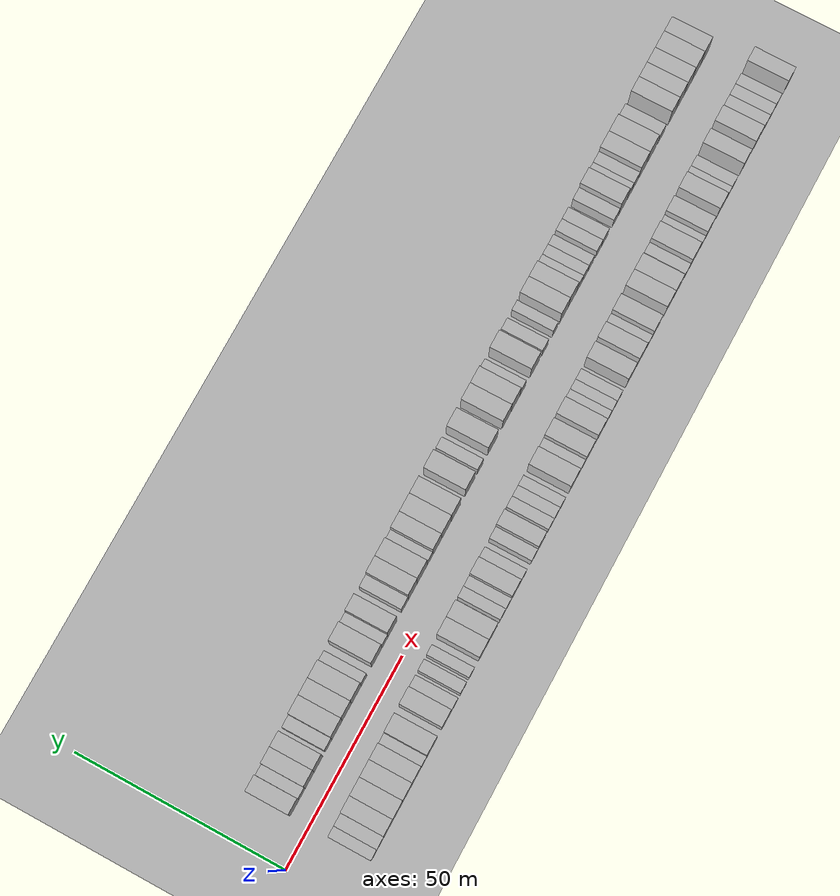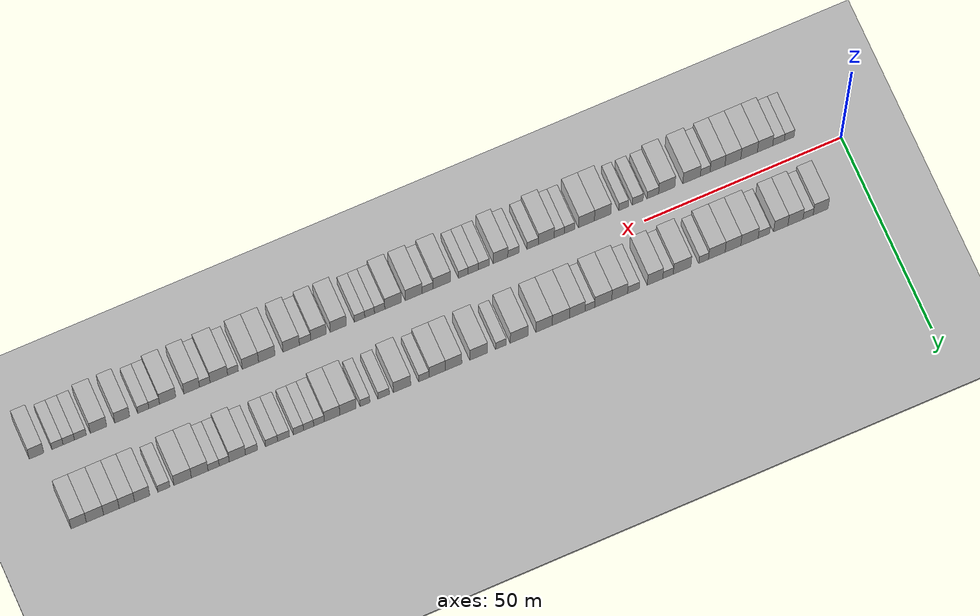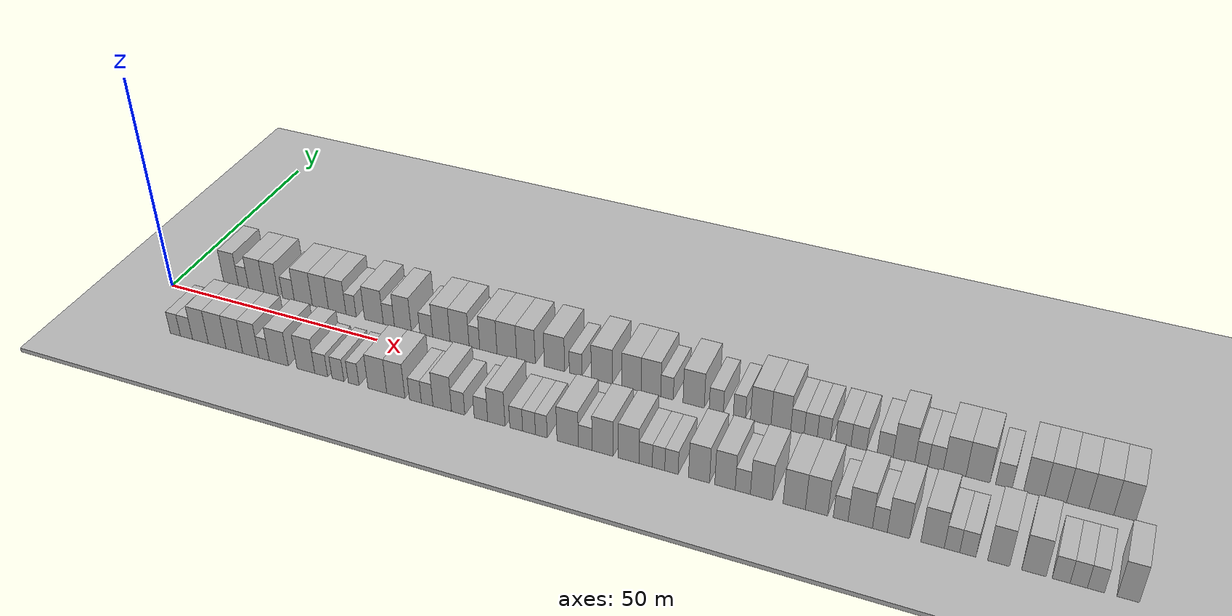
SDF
<?xml version="1.0" encoding="utf-8"?>

<sdf version="1.6">

   <world name="default">

      <gui fullscreen="0">

         <camera name="user_camera">

            <pose>-15 0 4.57585 0 0 0</pose>

            <view_controller>orbit</view_controller>

         </camera>

      </gui>

      <scene>

         <sky>

           <clouds>

             <speed>12</speed>

           </clouds>

         </sky>

         <ambient>0.4 0.4 0.4 1</ambient>

         <background>0.7 0.7 0.7 1</background>

         <shadows>1</shadows>

      </scene>

      <gravity>0 0 -9.8066</gravity>

      <magnetic_field>6e-06 2.3e-05 -4.2e-05</magnetic_field>

      <physics default="0" name="default_physics" type="ode">

         <ode>

            <solver>

               <type>quick</type>

               <iters>10</iters>

               <sor>1.0</sor>

               <use_dynamic_moi_rescaling>0</use_dynamic_moi_rescaling>

            </solver>

            <constraints>

               <cfm>0</cfm>

               <erp>0.2</erp>

               <contact_max_correcting_vel>100</contact_max_correcting_vel>

               <contact_surface_layer>0.001</contact_surface_layer>

            </constraints>

         </ode>

         <max_step_size>0.004</max_step_size>

         <real_time_factor>1</real_time_factor>

         <real_time_update_rate>250</real_time_update_rate>

      </physics>

      <light name="sun" type="directional">

         <cast_shadows>1</cast_shadows>

         <pose>0 0 10 0 0 0</pose>

         <diffuse>0.8 0.8 0.8 1</diffuse>

         <specular>0.2 0.2 0.2 1</specular>

         <attenuation>

            <range>1000</range>

            <constant>0.9</constant>

            <linear>0.01</linear>

            <quadratic>0.001</quadratic>

         </attenuation>

         <direction>-0.5 0.1 -0.9</direction>

      </light>

      <include>

         <name>ground_plane_1</name>

         <uri>model://HANNAS_ground_plane</uri>

         <pose>0 0 0  0 0 0</pose>

      </include>

      <include>

         <name>ground_plane_2</name>

         <uri>model://HANNAS_ground_plane</uri>

         <pose>100 0 0  0 0 0</pose>

      </include>

      <model name="building_1">

         <static>1</static>

         <pose frame="">11.8868 9.5000 0 0.000000 0.000000 1.570796</pose>

         <link name="link">

            <pose frame="">0 0 4.50 0 0 0</pose>

            <collision name="collision">

               <geometry>

                  <box>

                     <size>10.0000 3.7736 9.0000</size>

                  </box>

               </geometry>

               <max_contacts>10</max_contacts>

               <surface>

                  <contact>

                     <ode/>

                  </contact>

                  <bounce/>

                  <friction>

                     <torsional>

                        <ode/>

                     </torsional>

                     <ode/>

                  </friction>

               </surface>

            </collision>

            <visual name="visual">

               <cast_shadows>0</cast_shadows>

               <geometry>

                  <box>

                     <size>10.0000 3.7736 9.0000</size>

                  </box>

               </geometry>

               <material>

                  <script>

                     <uri>model://HANNAS_wall/materials/scripts</uri>

                     <uri>model://HANNAS_wall/materials/textures</uri>

                     <name>vrc/HANNAS_wall</name>

                  </script>

               </material>

            </visual>

            <self_collide>0</self_collide>

            <enable_wind>0</enable_wind>

            <kinematic>0</kinematic>

         </link>

      </model>

      <model name="building_2">

         <static>1</static>

         <pose frame="">15.0620 9.5000 0 0.000000 0.000000 1.570796</pose>

         <link name="link">

            <pose frame="">0 0 3.00 0 0 0</pose>

            <collision name="collision">

               <geometry>

                  <box>

                     <size>10.0000 2.5769 6.0000</size>

                  </box>

               </geometry>

               <max_contacts>10</max_contacts>

               <surface>

                  <contact>

                     <ode/>

                  </contact>

                  <bounce/>

                  <friction>

                     <torsional>

                        <ode/>

                     </torsional>

                     <ode/>

                  </friction>

               </surface>

            </collision>

            <visual name="visual">

               <cast_shadows>0</cast_shadows>

               <geometry>

                  <box>

                     <size>10.0000 2.5769 6.0000</size>

                  </box>

               </geometry>

               <material>

                  <script>

                     <uri>model://HANNAS_wall/materials/scripts</uri>

                     <uri>model://HANNAS_wall/materials/textures</uri>

                     <name>vrc/HANNAS_wall</name>

                  </script>

               </material>

            </visual>

            <self_collide>0</self_collide>

            <enable_wind>0</enable_wind>

            <kinematic>0</kinematic>

         </link>

      </model>

      <model name="building_3">

         <static>1</static>

         <pose frame="">18.2629 9.5000 0 0.000000 0.000000 1.570796</pose>

         <link name="link">

            <pose frame="">0 0 4.50 0 0 0</pose>

            <collision name="collision">

               <geometry>

                  <box>

                     <size>10.0000 3.8249 9.0000</size>

                  </box>

               </geometry>

               <max_contacts>10</max_contacts>

               <surface>

                  <contact>

                     <ode/>

                  </contact>

                  <bounce/>

                  <friction>

                     <torsional>

                        <ode/>

                     </torsional>

                     <ode/>

                  </friction>

               </surface>

            </collision>

            <visual name="visual">

               <cast_shadows>0</cast_shadows>

               <geometry>

                  <box>

                     <size>10.0000 3.8249 9.0000</size>

                  </box>

               </geometry>

               <material>

                  <script>

                     <uri>model://HANNAS_wall/materials/scripts</uri>

                     <uri>model://HANNAS_wall/materials/textures</uri>

                     <name>vrc/HANNAS_wall</name>

                  </script>

               </material>

            </visual>

            <self_collide>0</self_collide>

            <enable_wind>0</enable_wind>

            <kinematic>0</kinematic>

         </link>

      </model>

      <model name="building_4">

         <static>1</static>

         <pose frame="">21.9910 9.5000 0 0.000000 0.000000 1.570796</pose>

         <link name="link">

            <pose frame="">0 0 4.50 0 0 0</pose>

            <collision name="collision">

               <geometry>

                  <box>

                     <size>10.0000 3.6313 9.0000</size>

                  </box>

               </geometry>

               <max_contacts>10</max_contacts>

               <surface>

                  <contact>

                     <ode/>

                  </contact>

                  <bounce/>

                  <friction>

                     <torsional>

                        <ode/>

                     </torsional>

                     <ode/>

                  </friction>

               </surface>

            </collision>

            <visual name="visual">

               <cast_shadows>0</cast_shadows>

               <geometry>

                  <box>

                     <size>10.0000 3.6313 9.0000</size>

                  </box>

               </geometry>

               <material>

                  <script>

                     <uri>model://HANNAS_wall/materials/scripts</uri>

                     <uri>model://HANNAS_wall/materials/textures</uri>

                     <name>vrc/HANNAS_wall</name>

                  </script>

               </material>

            </visual>

            <self_collide>0</self_collide>

            <enable_wind>0</enable_wind>

            <kinematic>0</kinematic>

         </link>

      </model>

      <model name="building_5">

         <static>1</static>

         <pose frame="">26.2558 9.5000 0 0.000000 0.000000 1.570796</pose>

         <link name="link">

            <pose frame="">0 0 3.00 0 0 0</pose>

            <collision name="collision">

               <geometry>

                  <box>

                     <size>10.0000 2.8984 6.0000</size>

                  </box>

               </geometry>

               <max_contacts>10</max_contacts>

               <surface>

                  <contact>

                     <ode/>

                  </contact>

                  <bounce/>

                  <friction>

                     <torsional>

                        <ode/>

                     </torsional>

                     <ode/>

                  </friction>

               </surface>

            </collision>

            <visual name="visual">

               <cast_shadows>0</cast_shadows>

               <geometry>

                  <box>

                     <size>10.0000 2.8984 6.0000</size>

                  </box>

               </geometry>

               <material>

                  <script>

                     <uri>model://HANNAS_wall/materials/scripts</uri>

                     <uri>model://HANNAS_wall/materials/textures</uri>

                     <name>vrc/HANNAS_wall</name>

                  </script>

               </material>

            </visual>

            <self_collide>0</self_collide>

            <enable_wind>0</enable_wind>

            <kinematic>0</kinematic>

         </link>

      </model>

      <model name="building_6">

         <static>1</static>

         <pose frame="">29.9096 9.5000 0 0.000000 0.000000 1.570796</pose>

         <link name="link">

            <pose frame="">0 0 4.50 0 0 0</pose>

            <collision name="collision">

               <geometry>

                  <box>

                     <size>10.0000 4.4091 9.0000</size>

                  </box>

               </geometry>

               <max_contacts>10</max_contacts>

               <surface>

                  <contact>

                     <ode/>

                  </contact>

                  <bounce/>

                  <friction>

                     <torsional>

                        <ode/>

                     </torsional>

                     <ode/>

                  </friction>

               </surface>

            </collision>

            <visual name="visual">

               <cast_shadows>0</cast_shadows>

               <geometry>

                  <box>

                     <size>10.0000 4.4091 9.0000</size>

                  </box>

               </geometry>

               <material>

                  <script>

                     <uri>model://HANNAS_wall/materials/scripts</uri>

                     <uri>model://HANNAS_wall/materials/textures</uri>

                     <name>vrc/HANNAS_wall</name>

                  </script>

               </material>

            </visual>

            <self_collide>0</self_collide>

            <enable_wind>0</enable_wind>

            <kinematic>0</kinematic>

         </link>

      </model>

      <model name="building_7">

         <static>1</static>

         <pose frame="">34.0918 9.5000 0 0.000000 0.000000 1.570796</pose>

         <link name="link">

            <pose frame="">0 0 4.50 0 0 0</pose>

            <collision name="collision">

               <geometry>

                  <box>

                     <size>10.0000 3.9553 9.0000</size>

                  </box>

               </geometry>

               <max_contacts>10</max_contacts>

               <surface>

                  <contact>

                     <ode/>

                  </contact>

                  <bounce/>

                  <friction>

                     <torsional>

                        <ode/>

                     </torsional>

                     <ode/>

                  </friction>

               </surface>

            </collision>

            <visual name="visual">

               <cast_shadows>0</cast_shadows>

               <geometry>

                  <box>

                     <size>10.0000 3.9553 9.0000</size>

                  </box>

               </geometry>

               <material>

                  <script>

                     <uri>model://HANNAS_wall/materials/scripts</uri>

                     <uri>model://HANNAS_wall/materials/textures</uri>

                     <name>vrc/HANNAS_wall</name>

                  </script>

               </material>

            </visual>

            <self_collide>0</self_collide>

            <enable_wind>0</enable_wind>

            <kinematic>0</kinematic>

         </link>

      </model>

      <model name="building_8">

         <static>1</static>

         <pose frame="">38.1682 9.5000 0 0.000000 0.000000 1.570796</pose>

         <link name="link">

            <pose frame="">0 0 4.50 0 0 0</pose>

            <collision name="collision">

               <geometry>

                  <box>

                     <size>10.0000 4.1977 9.0000</size>

                  </box>

               </geometry>

               <max_contacts>10</max_contacts>

               <surface>

                  <contact>

                     <ode/>

                  </contact>

                  <bounce/>

                  <friction>

                     <torsional>

                        <ode/>

                     </torsional>

                     <ode/>

                  </friction>

               </surface>

            </collision>

            <visual name="visual">

               <cast_shadows>0</cast_shadows>

               <geometry>

                  <box>

                     <size>10.0000 4.1977 9.0000</size>

                  </box>

               </geometry>

               <material>

                  <script>

                     <uri>model://HANNAS_wall/materials/scripts</uri>

                     <uri>model://HANNAS_wall/materials/textures</uri>

                     <name>vrc/HANNAS_wall</name>

                  </script>

               </material>

            </visual>

            <self_collide>0</self_collide>

            <enable_wind>0</enable_wind>

            <kinematic>0</kinematic>

         </link>

      </model>

      <model name="building_9">

         <static>1</static>

         <pose frame="">41.4952 9.5000 0 0.000000 0.000000 1.570796</pose>

         <link name="link">

            <pose frame="">0 0 3.00 0 0 0</pose>

            <collision name="collision">

               <geometry>

                  <box>

                     <size>10.0000 2.4562 6.0000</size>

                  </box>

               </geometry>

               <max_contacts>10</max_contacts>

               <surface>

                  <contact>

                     <ode/>

                  </contact>

                  <bounce/>

                  <friction>

                     <torsional>

                        <ode/>

                     </torsional>

                     <ode/>

                  </friction>

               </surface>

            </collision>

            <visual name="visual">

               <cast_shadows>0</cast_shadows>

               <geometry>

                  <box>

                     <size>10.0000 2.4562 6.0000</size>

                  </box>

               </geometry>

               <material>

                  <script>

                     <uri>model://HANNAS_wall/materials/scripts</uri>

                     <uri>model://HANNAS_wall/materials/textures</uri>

                     <name>vrc/HANNAS_wall</name>

                  </script>

               </material>

            </visual>

            <self_collide>0</self_collide>

            <enable_wind>0</enable_wind>

            <kinematic>0</kinematic>

         </link>

      </model>

      <model name="building_10">

         <static>1</static>

         <pose frame="">46.9488 9.5000 0 0.000000 0.000000 1.570796</pose>

         <link name="link">

            <pose frame="">0 0 4.50 0 0 0</pose>

            <collision name="collision">

               <geometry>

                  <box>

                     <size>10.0000 4.4510 9.0000</size>

                  </box>

               </geometry>

               <max_contacts>10</max_contacts>

               <surface>

                  <contact>

                     <ode/>

                  </contact>

                  <bounce/>

                  <friction>

                     <torsional>

                        <ode/>

                     </torsional>

                     <ode/>

                  </friction>

               </surface>

            </collision>

            <visual name="visual">

               <cast_shadows>0</cast_shadows>

               <geometry>

                  <box>

                     <size>10.0000 4.4510 9.0000</size>

                  </box>

               </geometry>

               <material>

                  <script>

                     <uri>model://HANNAS_wall/materials/scripts</uri>

                     <uri>model://HANNAS_wall/materials/textures</uri>

                     <name>vrc/HANNAS_wall</name>

                  </script>

               </material>

            </visual>

            <self_collide>0</self_collide>

            <enable_wind>0</enable_wind>

            <kinematic>0</kinematic>

         </link>

      </model>

      <model name="building_11">

         <static>1</static>

         <pose frame="">50.4869 9.5000 0 0.000000 0.000000 1.570796</pose>

         <link name="link">

            <pose frame="">0 0 3.00 0 0 0</pose>

            <collision name="collision">

               <geometry>

                  <box>

                     <size>10.0000 2.6252 6.0000</size>

                  </box>

               </geometry>

               <max_contacts>10</max_contacts>

               <surface>

                  <contact>

                     <ode/>

                  </contact>

                  <bounce/>

                  <friction>

                     <torsional>

                        <ode/>

                     </torsional>

                     <ode/>

                  </friction>

               </surface>

            </collision>

            <visual name="visual">

               <cast_shadows>0</cast_shadows>

               <geometry>

                  <box>

                     <size>10.0000 2.6252 6.0000</size>

                  </box>

               </geometry>

               <material>

                  <script>

                     <uri>model://HANNAS_wall/materials/scripts</uri>

                     <uri>model://HANNAS_wall/materials/textures</uri>

                     <name>vrc/HANNAS_wall</name>

                  </script>

               </material>

            </visual>

            <self_collide>0</self_collide>

            <enable_wind>0</enable_wind>

            <kinematic>0</kinematic>

         </link>

      </model>

      <model name="building_12">

         <static>1</static>

         <pose frame="">53.7622 9.5000 0 0.000000 0.000000 1.570796</pose>

         <link name="link">

            <pose frame="">0 0 4.50 0 0 0</pose>

            <collision name="collision">

               <geometry>

                  <box>

                     <size>10.0000 3.9254 9.0000</size>

                  </box>

               </geometry>

               <max_contacts>10</max_contacts>

               <surface>

                  <contact>

                     <ode/>

                  </contact>

                  <bounce/>

                  <friction>

                     <torsional>

                        <ode/>

                     </torsional>

                     <ode/>

                  </friction>

               </surface>

            </collision>

            <visual name="visual">

               <cast_shadows>0</cast_shadows>

               <geometry>

                  <box>

                     <size>10.0000 3.9254 9.0000</size>

                  </box>

               </geometry>

               <material>

                  <script>

                     <uri>model://HANNAS_wall/materials/scripts</uri>

                     <uri>model://HANNAS_wall/materials/textures</uri>

                     <name>vrc/HANNAS_wall</name>

                  </script>

               </material>

            </visual>

            <self_collide>0</self_collide>

            <enable_wind>0</enable_wind>

            <kinematic>0</kinematic>

         </link>

      </model>

      <model name="building_13">

         <static>1</static>

         <pose frame="">59.2164 9.5000 0 0.000000 0.000000 1.570796</pose>

         <link name="link">

            <pose frame="">0 0 3.00 0 0 0</pose>

            <collision name="collision">

               <geometry>

                  <box>

                     <size>10.0000 2.9829 6.0000</size>

                  </box>

               </geometry>

               <max_contacts>10</max_contacts>

               <surface>

                  <contact>

                     <ode/>

                  </contact>

                  <bounce/>

                  <friction>

                     <torsional>

                        <ode/>

                     </torsional>

                     <ode/>

                  </friction>

               </surface>

            </collision>

            <visual name="visual">

               <cast_shadows>0</cast_shadows>

               <geometry>

                  <box>

                     <size>10.0000 2.9829 6.0000</size>

                  </box>

               </geometry>

               <material>

                  <script>

                     <uri>model://HANNAS_wall/materials/scripts</uri>

                     <uri>model://HANNAS_wall/materials/textures</uri>

                     <name>vrc/HANNAS_wall</name>

                  </script>

               </material>

            </visual>

            <self_collide>0</self_collide>

            <enable_wind>0</enable_wind>

            <kinematic>0</kinematic>

         </link>

      </model>

      <model name="building_14">

         <static>1</static>

         <pose frame="">62.6915 9.5000 0 0.000000 0.000000 1.570796</pose>

         <link name="link">

            <pose frame="">0 0 4.50 0 0 0</pose>

            <collision name="collision">

               <geometry>

                  <box>

                     <size>10.0000 3.9674 9.0000</size>

                  </box>

               </geometry>

               <max_contacts>10</max_contacts>

               <surface>

                  <contact>

                     <ode/>

                  </contact>

                  <bounce/>

                  <friction>

                     <torsional>

                        <ode/>

                     </torsional>

                     <ode/>

                  </friction>

               </surface>

            </collision>

            <visual name="visual">

               <cast_shadows>0</cast_shadows>

               <geometry>

                  <box>

                     <size>10.0000 3.9674 9.0000</size>

                  </box>

               </geometry>

               <material>

                  <script>

                     <uri>model://HANNAS_wall/materials/scripts</uri>

                     <uri>model://HANNAS_wall/materials/textures</uri>

                     <name>vrc/HANNAS_wall</name>

                  </script>

               </material>

            </visual>

            <self_collide>0</self_collide>

            <enable_wind>0</enable_wind>

            <kinematic>0</kinematic>

         </link>

      </model>

      <model name="building_15">

         <static>1</static>

         <pose frame="">66.8374 9.5000 0 0.000000 0.000000 1.570796</pose>

         <link name="link">

            <pose frame="">0 0 4.50 0 0 0</pose>

            <collision name="collision">

               <geometry>

                  <box>

                     <size>10.0000 4.3243 9.0000</size>

                  </box>

               </geometry>

               <max_contacts>10</max_contacts>

               <surface>

                  <contact>

                     <ode/>

                  </contact>

                  <bounce/>

                  <friction>

                     <torsional>

                        <ode/>

                     </torsional>

                     <ode/>

                  </friction>

               </surface>

            </collision>

            <visual name="visual">

               <cast_shadows>0</cast_shadows>

               <geometry>

                  <box>

                     <size>10.0000 4.3243 9.0000</size>

                  </box>

               </geometry>

               <material>

                  <script>

                     <uri>model://HANNAS_wall/materials/scripts</uri>

                     <uri>model://HANNAS_wall/materials/textures</uri>

                     <name>vrc/HANNAS_wall</name>

                  </script>

               </material>

            </visual>

            <self_collide>0</self_collide>

            <enable_wind>0</enable_wind>

            <kinematic>0</kinematic>

         </link>

      </model>

      <model name="building_16">

         <static>1</static>

         <pose frame="">70.2006 9.5000 0 0.000000 0.000000 1.570796</pose>

         <link name="link">

            <pose frame="">0 0 3.00 0 0 0</pose>

            <collision name="collision">

               <geometry>

                  <box>

                     <size>10.0000 2.4023 6.0000</size>

                  </box>

               </geometry>

               <max_contacts>10</max_contacts>

               <surface>

                  <contact>

                     <ode/>

                  </contact>

                  <bounce/>

                  <friction>

                     <torsional>

                        <ode/>

                     </torsional>

                     <ode/>

                  </friction>

               </surface>

            </collision>

            <visual name="visual">

               <cast_shadows>0</cast_shadows>

               <geometry>

                  <box>

                     <size>10.0000 2.4023 6.0000</size>

                  </box>

               </geometry>

               <material>

                  <script>

                     <uri>model://HANNAS_wall/materials/scripts</uri>

                     <uri>model://HANNAS_wall/materials/textures</uri>

                     <name>vrc/HANNAS_wall</name>

                  </script>

               </material>

            </visual>

            <self_collide>0</self_collide>

            <enable_wind>0</enable_wind>

            <kinematic>0</kinematic>

         </link>

      </model>

      <model name="building_17">

         <static>1</static>

         <pose frame="">73.3415 9.5000 0 0.000000 0.000000 1.570796</pose>

         <link name="link">

            <pose frame="">0 0 4.50 0 0 0</pose>

            <collision name="collision">

               <geometry>

                  <box>

                     <size>10.0000 3.8795 9.0000</size>

                  </box>

               </geometry>

               <max_contacts>10</max_contacts>

               <surface>

                  <contact>

                     <ode/>

                  </contact>

                  <bounce/>

                  <friction>

                     <torsional>

                        <ode/>

                     </torsional>

                     <ode/>

                  </friction>

               </surface>

            </collision>

            <visual name="visual">

               <cast_shadows>0</cast_shadows>

               <geometry>

                  <box>

                     <size>10.0000 3.8795 9.0000</size>

                  </box>

               </geometry>

               <material>

                  <script>

                     <uri>model://HANNAS_wall/materials/scripts</uri>

                     <uri>model://HANNAS_wall/materials/textures</uri>

                     <name>vrc/HANNAS_wall</name>

                  </script>

               </material>

            </visual>

            <self_collide>0</self_collide>

            <enable_wind>0</enable_wind>

            <kinematic>0</kinematic>

         </link>

      </model>

      <model name="building_18">

         <static>1</static>

         <pose frame="">77.4658 9.5000 0 0.000000 0.000000 1.570796</pose>

         <link name="link">

            <pose frame="">0 0 4.50 0 0 0</pose>

            <collision name="collision">

               <geometry>

                  <box>

                     <size>10.0000 4.3690 9.0000</size>

                  </box>

               </geometry>

               <max_contacts>10</max_contacts>

               <surface>

                  <contact>

                     <ode/>

                  </contact>

                  <bounce/>

                  <friction>

                     <torsional>

                        <ode/>

                     </torsional>

                     <ode/>

                  </friction>

               </surface>

            </collision>

            <visual name="visual">

               <cast_shadows>0</cast_shadows>

               <geometry>

                  <box>

                     <size>10.0000 4.3690 9.0000</size>

                  </box>

               </geometry>

               <material>

                  <script>

                     <uri>model://HANNAS_wall/materials/scripts</uri>

                     <uri>model://HANNAS_wall/materials/textures</uri>

                     <name>vrc/HANNAS_wall</name>

                  </script>

               </material>

            </visual>

            <self_collide>0</self_collide>

            <enable_wind>0</enable_wind>

            <kinematic>0</kinematic>

         </link>

      </model>

      <model name="building_19">

         <static>1</static>

         <pose frame="">81.7029 9.5000 0 0.000000 0.000000 1.570796</pose>

         <link name="link">

            <pose frame="">0 0 4.50 0 0 0</pose>

            <collision name="collision">

               <geometry>

                  <box>

                     <size>10.0000 4.1053 9.0000</size>

                  </box>

               </geometry>

               <max_contacts>10</max_contacts>

               <surface>

                  <contact>

                     <ode/>

                  </contact>

                  <bounce/>

                  <friction>

                     <torsional>

                        <ode/>

                     </torsional>

                     <ode/>

                  </friction>

               </surface>

            </collision>

            <visual name="visual">

               <cast_shadows>0</cast_shadows>

               <geometry>

                  <box>

                     <size>10.0000 4.1053 9.0000</size>

                  </box>

               </geometry>

               <material>

                  <script>

                     <uri>model://HANNAS_wall/materials/scripts</uri>

                     <uri>model://HANNAS_wall/materials/textures</uri>

                     <name>vrc/HANNAS_wall</name>

                  </script>

               </material>

            </visual>

            <self_collide>0</self_collide>

            <enable_wind>0</enable_wind>

            <kinematic>0</kinematic>

         </link>

      </model>

      <model name="building_20">

         <static>1</static>

         <pose frame="">87.9693 9.5000 0 0.000000 0.000000 1.570796</pose>

         <link name="link">

            <pose frame="">0 0 4.50 0 0 0</pose>

            <collision name="collision">

               <geometry>

                  <box>

                     <size>10.0000 4.4275 9.0000</size>

                  </box>

               </geometry>

               <max_contacts>10</max_contacts>

               <surface>

                  <contact>

                     <ode/>

                  </contact>

                  <bounce/>

                  <friction>

                     <torsional>

                        <ode/>

                     </torsional>

                     <ode/>

                  </friction>

               </surface>

            </collision>

            <visual name="visual">

               <cast_shadows>0</cast_shadows>

               <geometry>

                  <box>

                     <size>10.0000 4.4275 9.0000</size>

                  </box>

               </geometry>

               <material>

                  <script>

                     <uri>model://HANNAS_wall/materials/scripts</uri>

                     <uri>model://HANNAS_wall/materials/textures</uri>

                     <name>vrc/HANNAS_wall</name>

                  </script>

               </material>

            </visual>

            <self_collide>0</self_collide>

            <enable_wind>0</enable_wind>

            <kinematic>0</kinematic>

         </link>

      </model>

      <model name="building_21">

         <static>1</static>

         <pose frame="">92.5368 9.5000 0 0.000000 0.000000 1.570796</pose>

         <link name="link">

            <pose frame="">0 0 3.00 0 0 0</pose>

            <collision name="collision">

               <geometry>

                  <box>

                     <size>10.0000 2.7074 6.0000</size>

                  </box>

               </geometry>

               <max_contacts>10</max_contacts>

               <surface>

                  <contact>

                     <ode/>

                  </contact>

                  <bounce/>

                  <friction>

                     <torsional>

                        <ode/>

                     </torsional>

                     <ode/>

                  </friction>

               </surface>

            </collision>

            <visual name="visual">

               <cast_shadows>0</cast_shadows>

               <geometry>

                  <box>

                     <size>10.0000 2.7074 6.0000</size>

                  </box>

               </geometry>

               <material>

                  <script>

                     <uri>model://HANNAS_wall/materials/scripts</uri>

                     <uri>model://HANNAS_wall/materials/textures</uri>

                     <name>vrc/HANNAS_wall</name>

                  </script>

               </material>

            </visual>

            <self_collide>0</self_collide>

            <enable_wind>0</enable_wind>

            <kinematic>0</kinematic>

         </link>

      </model>

      <model name="building_22">

         <static>1</static>

         <pose frame="">98.1123 9.5000 0 0.000000 0.000000 1.570796</pose>

         <link name="link">

            <pose frame="">0 0 4.50 0 0 0</pose>

            <collision name="collision">

               <geometry>

                  <box>

                     <size>10.0000 4.4437 9.0000</size>

                  </box>

               </geometry>

               <max_contacts>10</max_contacts>

               <surface>

                  <contact>

                     <ode/>

                  </contact>

                  <bounce/>

                  <friction>

                     <torsional>

                        <ode/>

                     </torsional>

                     <ode/>

                  </friction>

               </surface>

            </collision>

            <visual name="visual">

               <cast_shadows>0</cast_shadows>

               <geometry>

                  <box>

                     <size>10.0000 4.4437 9.0000</size>

                  </box>

               </geometry>

               <material>

                  <script>

                     <uri>model://HANNAS_wall/materials/scripts</uri>

                     <uri>model://HANNAS_wall/materials/textures</uri>

                     <name>vrc/HANNAS_wall</name>

                  </script>

               </material>

            </visual>

            <self_collide>0</self_collide>

            <enable_wind>0</enable_wind>

            <kinematic>0</kinematic>

         </link>

      </model>

      <model name="building_23">

         <static>1</static>

         <pose frame="">104.3862 9.5000 0 0.000000 0.000000 1.570796</pose>

         <link name="link">

            <pose frame="">0 0 4.50 0 0 0</pose>

            <collision name="collision">

               <geometry>

                  <box>

                     <size>10.0000 4.1040 9.0000</size>

                  </box>

               </geometry>

               <max_contacts>10</max_contacts>

               <surface>

                  <contact>

                     <ode/>

                  </contact>

                  <bounce/>

                  <friction>

                     <torsional>

                        <ode/>

                     </torsional>

                     <ode/>

                  </friction>

               </surface>

            </collision>

            <visual name="visual">

               <cast_shadows>0</cast_shadows>

               <geometry>

                  <box>

                     <size>10.0000 4.1040 9.0000</size>

                  </box>

               </geometry>

               <material>

                  <script>

                     <uri>model://HANNAS_wall/materials/scripts</uri>

                     <uri>model://HANNAS_wall/materials/textures</uri>

                     <name>vrc/HANNAS_wall</name>

                  </script>

               </material>

            </visual>

            <self_collide>0</self_collide>

            <enable_wind>0</enable_wind>

            <kinematic>0</kinematic>

         </link>

      </model>

      <model name="building_24">

         <static>1</static>

         <pose frame="">108.4882 9.5000 0 0.000000 0.000000 1.570796</pose>

         <link name="link">

            <pose frame="">0 0 4.50 0 0 0</pose>

            <collision name="collision">

               <geometry>

                  <box>

                     <size>10.0000 4.1000 9.0000</size>

                  </box>

               </geometry>

               <max_contacts>10</max_contacts>

               <surface>

                  <contact>

                     <ode/>

                  </contact>

                  <bounce/>

                  <friction>

                     <torsional>

                        <ode/>

                     </torsional>

                     <ode/>

                  </friction>

               </surface>

            </collision>

            <visual name="visual">

               <cast_shadows>0</cast_shadows>

               <geometry>

                  <box>

                     <size>10.0000 4.1000 9.0000</size>

                  </box>

               </geometry>

               <material>

                  <script>

                     <uri>model://HANNAS_wall/materials/scripts</uri>

                     <uri>model://HANNAS_wall/materials/textures</uri>

                     <name>vrc/HANNAS_wall</name>

                  </script>

               </material>

            </visual>

            <self_collide>0</self_collide>

            <enable_wind>0</enable_wind>

            <kinematic>0</kinematic>

         </link>

      </model>

      <model name="building_25">

         <static>1</static>

         <pose frame="">111.8313 9.5000 0 0.000000 0.000000 1.570796</pose>

         <link name="link">

            <pose frame="">0 0 3.00 0 0 0</pose>

            <collision name="collision">

               <geometry>

                  <box>

                     <size>10.0000 2.5863 6.0000</size>

                  </box>

               </geometry>

               <max_contacts>10</max_contacts>

               <surface>

                  <contact>

                     <ode/>

                  </contact>

                  <bounce/>

                  <friction>

                     <torsional>

                        <ode/>

                     </torsional>

                     <ode/>

                  </friction>

               </surface>

            </collision>

            <visual name="visual">

               <cast_shadows>0</cast_shadows>

               <geometry>

                  <box>

                     <size>10.0000 2.5863 6.0000</size>

                  </box>

               </geometry>

               <material>

                  <script>

                     <uri>model://HANNAS_wall/materials/scripts</uri>

                     <uri>model://HANNAS_wall/materials/textures</uri>

                     <name>vrc/HANNAS_wall</name>

                  </script>

               </material>

            </visual>

            <self_collide>0</self_collide>

            <enable_wind>0</enable_wind>

            <kinematic>0</kinematic>

         </link>

      </model>

      <model name="building_26">

         <static>1</static>

         <pose frame="">117.2905 9.5000 0 0.000000 0.000000 1.570796</pose>

         <link name="link">

            <pose frame="">0 0 4.50 0 0 0</pose>

            <collision name="collision">

               <geometry>

                  <box>

                     <size>10.0000 4.3321 9.0000</size>

                  </box>

               </geometry>

               <max_contacts>10</max_contacts>

               <surface>

                  <contact>

                     <ode/>

                  </contact>

                  <bounce/>

                  <friction>

                     <torsional>

                        <ode/>

                     </torsional>

                     <ode/>

                  </friction>

               </surface>

            </collision>

            <visual name="visual">

               <cast_shadows>0</cast_shadows>

               <geometry>

                  <box>

                     <size>10.0000 4.3321 9.0000</size>

                  </box>

               </geometry>

               <material>

                  <script>

                     <uri>model://HANNAS_wall/materials/scripts</uri>

                     <uri>model://HANNAS_wall/materials/textures</uri>

                     <name>vrc/HANNAS_wall</name>

                  </script>

               </material>

            </visual>

            <self_collide>0</self_collide>

            <enable_wind>0</enable_wind>

            <kinematic>0</kinematic>

         </link>

      </model>

      <model name="building_27">

         <static>1</static>

         <pose frame="">121.8870 9.5000 0 0.000000 0.000000 1.570796</pose>

         <link name="link">

            <pose frame="">0 0 3.00 0 0 0</pose>

            <collision name="collision">

               <geometry>

                  <box>

                     <size>10.0000 2.8608 6.0000</size>

                  </box>

               </geometry>

               <max_contacts>10</max_contacts>

               <surface>

                  <contact>

                     <ode/>

                  </contact>

                  <bounce/>

                  <friction>

                     <torsional>

                        <ode/>

                     </torsional>

                     <ode/>

                  </friction>

               </surface>

            </collision>

            <visual name="visual">

               <cast_shadows>0</cast_shadows>

               <geometry>

                  <box>

                     <size>10.0000 2.8608 6.0000</size>

                  </box>

               </geometry>

               <material>

                  <script>

                     <uri>model://HANNAS_wall/materials/scripts</uri>

                     <uri>model://HANNAS_wall/materials/textures</uri>

                     <name>vrc/HANNAS_wall</name>

                  </script>

               </material>

            </visual>

            <self_collide>0</self_collide>

            <enable_wind>0</enable_wind>

            <kinematic>0</kinematic>

         </link>

      </model>

      <model name="building_28">

         <static>1</static>

         <pose frame="">126.5355 9.5000 0 0.000000 0.000000 1.570796</pose>

         <link name="link">

            <pose frame="">0 0 3.00 0 0 0</pose>

            <collision name="collision">

               <geometry>

                  <box>

                     <size>10.0000 2.4363 6.0000</size>

                  </box>

               </geometry>

               <max_contacts>10</max_contacts>

               <surface>

                  <contact>

                     <ode/>

                  </contact>

                  <bounce/>

                  <friction>

                     <torsional>

                        <ode/>

                     </torsional>

                     <ode/>

                  </friction>

               </surface>

            </collision>

            <visual name="visual">

               <cast_shadows>0</cast_shadows>

               <geometry>

                  <box>

                     <size>10.0000 2.4363 6.0000</size>

                  </box>

               </geometry>

               <material>

                  <script>

                     <uri>model://HANNAS_wall/materials/scripts</uri>

                     <uri>model://HANNAS_wall/materials/textures</uri>

                     <name>vrc/HANNAS_wall</name>

                  </script>

               </material>

            </visual>

            <self_collide>0</self_collide>

            <enable_wind>0</enable_wind>

            <kinematic>0</kinematic>

         </link>

      </model>

      <model name="building_29">

         <static>1</static>

         <pose frame="">130.7886 9.5000 0 0.000000 0.000000 1.570796</pose>

         <link name="link">

            <pose frame="">0 0 4.50 0 0 0</pose>

            <collision name="collision">

               <geometry>

                  <box>

                     <size>10.0000 4.0701 9.0000</size>

                  </box>

               </geometry>

               <max_contacts>10</max_contacts>

               <surface>

                  <contact>

                     <ode/>

                  </contact>

                  <bounce/>

                  <friction>

                     <torsional>

                        <ode/>

                     </torsional>

                     <ode/>

                  </friction>

               </surface>

            </collision>

            <visual name="visual">

               <cast_shadows>0</cast_shadows>

               <geometry>

                  <box>

                     <size>10.0000 4.0701 9.0000</size>

                  </box>

               </geometry>

               <material>

                  <script>

                     <uri>model://HANNAS_wall/materials/scripts</uri>

                     <uri>model://HANNAS_wall/materials/textures</uri>

                     <name>vrc/HANNAS_wall</name>

                  </script>

               </material>

            </visual>

            <self_collide>0</self_collide>

            <enable_wind>0</enable_wind>

            <kinematic>0</kinematic>

         </link>

      </model>

      <model name="building_30">

         <static>1</static>

         <pose frame="">134.7658 9.5000 0 0.000000 0.000000 1.570796</pose>

         <link name="link">

            <pose frame="">0 0 4.50 0 0 0</pose>

            <collision name="collision">

               <geometry>

                  <box>

                     <size>10.0000 3.8842 9.0000</size>

                  </box>

               </geometry>

               <max_contacts>10</max_contacts>

               <surface>

                  <contact>

                     <ode/>

                  </contact>

                  <bounce/>

                  <friction>

                     <torsional>

                        <ode/>

                     </torsional>

                     <ode/>

                  </friction>

               </surface>

            </collision>

            <visual name="visual">

               <cast_shadows>0</cast_shadows>

               <geometry>

                  <box>

                     <size>10.0000 3.8842 9.0000</size>

                  </box>

               </geometry>

               <material>

                  <script>

                     <uri>model://HANNAS_wall/materials/scripts</uri>

                     <uri>model://HANNAS_wall/materials/textures</uri>

                     <name>vrc/HANNAS_wall</name>

                  </script>

               </material>

            </visual>

            <self_collide>0</self_collide>

            <enable_wind>0</enable_wind>

            <kinematic>0</kinematic>

         </link>

      </model>

      <model name="building_31">

         <static>1</static>

         <pose frame="">138.0191 9.5000 0 0.000000 0.000000 1.570796</pose>

         <link name="link">

            <pose frame="">0 0 3.00 0 0 0</pose>

            <collision name="collision">

               <geometry>

                  <box>

                     <size>10.0000 2.6223 6.0000</size>

                  </box>

               </geometry>

               <max_contacts>10</max_contacts>

               <surface>

                  <contact>

                     <ode/>

                  </contact>

                  <bounce/>

                  <friction>

                     <torsional>

                        <ode/>

                     </torsional>

                     <ode/>

                  </friction>

               </surface>

            </collision>

            <visual name="visual">

               <cast_shadows>0</cast_shadows>

               <geometry>

                  <box>

                     <size>10.0000 2.6223 6.0000</size>

                  </box>

               </geometry>

               <material>

                  <script>

                     <uri>model://HANNAS_wall/materials/scripts</uri>

                     <uri>model://HANNAS_wall/materials/textures</uri>

                     <name>vrc/HANNAS_wall</name>

                  </script>

               </material>

            </visual>

            <self_collide>0</self_collide>

            <enable_wind>0</enable_wind>

            <kinematic>0</kinematic>

         </link>

      </model>

      <model name="building_32">

         <static>1</static>

         <pose frame="">140.6083 9.5000 0 0.000000 0.000000 1.570796</pose>

         <link name="link">

            <pose frame="">0 0 3.00 0 0 0</pose>

            <collision name="collision">

               <geometry>

                  <box>

                     <size>10.0000 2.5561 6.0000</size>

                  </box>

               </geometry>

               <max_contacts>10</max_contacts>

               <surface>

                  <contact>

                     <ode/>

                  </contact>

                  <bounce/>

                  <friction>

                     <torsional>

                        <ode/>

                     </torsional>

                     <ode/>

                  </friction>

               </surface>

            </collision>

            <visual name="visual">

               <cast_shadows>0</cast_shadows>

               <geometry>

                  <box>

                     <size>10.0000 2.5561 6.0000</size>

                  </box>

               </geometry>

               <material>

                  <script>

                     <uri>model://HANNAS_wall/materials/scripts</uri>

                     <uri>model://HANNAS_wall/materials/textures</uri>

                     <name>vrc/HANNAS_wall</name>

                  </script>

               </material>

            </visual>

            <self_collide>0</self_collide>

            <enable_wind>0</enable_wind>

            <kinematic>0</kinematic>

         </link>

      </model>

      <model name="building_33">

         <static>1</static>

         <pose frame="">143.1384 9.5000 0 0.000000 0.000000 1.570796</pose>

         <link name="link">

            <pose frame="">0 0 3.00 0 0 0</pose>

            <collision name="collision">

               <geometry>

                  <box>

                     <size>10.0000 2.5040 6.0000</size>

                  </box>

               </geometry>

               <max_contacts>10</max_contacts>

               <surface>

                  <contact>

                     <ode/>

                  </contact>

                  <bounce/>

                  <friction>

                     <torsional>

                        <ode/>

                     </torsional>

                     <ode/>

                  </friction>

               </surface>

            </collision>

            <visual name="visual">

               <cast_shadows>0</cast_shadows>

               <geometry>

                  <box>

                     <size>10.0000 2.5040 6.0000</size>

                  </box>

               </geometry>

               <material>

                  <script>

                     <uri>model://HANNAS_wall/materials/scripts</uri>

                     <uri>model://HANNAS_wall/materials/textures</uri>

                     <name>vrc/HANNAS_wall</name>

                  </script>

               </material>

            </visual>

            <self_collide>0</self_collide>

            <enable_wind>0</enable_wind>

            <kinematic>0</kinematic>

         </link>

      </model>

      <model name="building_34">

         <static>1</static>

         <pose frame="">146.8678 9.5000 0 0.000000 0.000000 1.570796</pose>

         <link name="link">

            <pose frame="">0 0 3.00 0 0 0</pose>

            <collision name="collision">

               <geometry>

                  <box>

                     <size>10.0000 2.9549 6.0000</size>

                  </box>

               </geometry>

               <max_contacts>10</max_contacts>

               <surface>

                  <contact>

                     <ode/>

                  </contact>

                  <bounce/>

                  <friction>

                     <torsional>

                        <ode/>

                     </torsional>

                     <ode/>

                  </friction>

               </surface>

            </collision>

            <visual name="visual">

               <cast_shadows>0</cast_shadows>

               <geometry>

                  <box>

                     <size>10.0000 2.9549 6.0000</size>

                  </box>

               </geometry>

               <material>

                  <script>

                     <uri>model://HANNAS_wall/materials/scripts</uri>

                     <uri>model://HANNAS_wall/materials/textures</uri>

                     <name>vrc/HANNAS_wall</name>

                  </script>

               </material>

            </visual>

            <self_collide>0</self_collide>

            <enable_wind>0</enable_wind>

            <kinematic>0</kinematic>

         </link>

      </model>

      <model name="building_35">

         <static>1</static>

         <pose frame="">149.8399 9.5000 0 0.000000 0.000000 1.570796</pose>

         <link name="link">

            <pose frame="">0 0 3.00 0 0 0</pose>

            <collision name="collision">

               <geometry>

                  <box>

                     <size>10.0000 2.9893 6.0000</size>

                  </box>

               </geometry>

               <max_contacts>10</max_contacts>

               <surface>

                  <contact>

                     <ode/>

                  </contact>

                  <bounce/>

                  <friction>

                     <torsional>

                        <ode/>

                     </torsional>

                     <ode/>

                  </friction>

               </surface>

            </collision>

            <visual name="visual">

               <cast_shadows>0</cast_shadows>

               <geometry>

                  <box>

                     <size>10.0000 2.9893 6.0000</size>

                  </box>

               </geometry>

               <material>

                  <script>

                     <uri>model://HANNAS_wall/materials/scripts</uri>

                     <uri>model://HANNAS_wall/materials/textures</uri>

                     <name>vrc/HANNAS_wall</name>

                  </script>

               </material>

            </visual>

            <self_collide>0</self_collide>

            <enable_wind>0</enable_wind>

            <kinematic>0</kinematic>

         </link>

      </model>

      <model name="building_36">

         <static>1</static>

         <pose frame="">154.8309 9.5000 0 0.000000 0.000000 1.570796</pose>

         <link name="link">

            <pose frame="">0 0 3.00 0 0 0</pose>

            <collision name="collision">

               <geometry>

                  <box>

                     <size>10.0000 2.9926 6.0000</size>

                  </box>

               </geometry>

               <max_contacts>10</max_contacts>

               <surface>

                  <contact>

                     <ode/>

                  </contact>

                  <bounce/>

                  <friction>

                     <torsional>

                        <ode/>

                     </torsional>

                     <ode/>

                  </friction>

               </surface>

            </collision>

            <visual name="visual">

               <cast_shadows>0</cast_shadows>

               <geometry>

                  <box>

                     <size>10.0000 2.9926 6.0000</size>

                  </box>

               </geometry>

               <material>

                  <script>

                     <uri>model://HANNAS_wall/materials/scripts</uri>

                     <uri>model://HANNAS_wall/materials/textures</uri>

                     <name>vrc/HANNAS_wall</name>

                  </script>

               </material>

            </visual>

            <self_collide>0</self_collide>

            <enable_wind>0</enable_wind>

            <kinematic>0</kinematic>

         </link>

      </model>

      <model name="building_37">

         <static>1</static>

         <pose frame="">158.3484 9.5000 0 0.000000 0.000000 1.570796</pose>

         <link name="link">

            <pose frame="">0 0 4.50 0 0 0</pose>

            <collision name="collision">

               <geometry>

                  <box>

                     <size>10.0000 4.0424 9.0000</size>

                  </box>

               </geometry>

               <max_contacts>10</max_contacts>

               <surface>

                  <contact>

                     <ode/>

                  </contact>

                  <bounce/>

                  <friction>

                     <torsional>

                        <ode/>

                     </torsional>

                     <ode/>

                  </friction>

               </surface>

            </collision>

            <visual name="visual">

               <cast_shadows>0</cast_shadows>

               <geometry>

                  <box>

                     <size>10.0000 4.0424 9.0000</size>

                  </box>

               </geometry>

               <material>

                  <script>

                     <uri>model://HANNAS_wall/materials/scripts</uri>

                     <uri>model://HANNAS_wall/materials/textures</uri>

                     <name>vrc/HANNAS_wall</name>

                  </script>

               </material>

            </visual>

            <self_collide>0</self_collide>

            <enable_wind>0</enable_wind>

            <kinematic>0</kinematic>

         </link>

      </model>

      <model name="building_38">

         <static>1</static>

         <pose frame="">161.6100 9.5000 0 0.000000 0.000000 1.570796</pose>

         <link name="link">

            <pose frame="">0 0 3.00 0 0 0</pose>

            <collision name="collision">

               <geometry>

                  <box>

                     <size>10.0000 2.4809 6.0000</size>

                  </box>

               </geometry>

               <max_contacts>10</max_contacts>

               <surface>

                  <contact>

                     <ode/>

                  </contact>

                  <bounce/>

                  <friction>

                     <torsional>

                        <ode/>

                     </torsional>

                     <ode/>

                  </friction>

               </surface>

            </collision>

            <visual name="visual">

               <cast_shadows>0</cast_shadows>

               <geometry>

                  <box>

                     <size>10.0000 2.4809 6.0000</size>

                  </box>

               </geometry>

               <material>

                  <script>

                     <uri>model://HANNAS_wall/materials/scripts</uri>

                     <uri>model://HANNAS_wall/materials/textures</uri>

                     <name>vrc/HANNAS_wall</name>

                  </script>

               </material>

            </visual>

            <self_collide>0</self_collide>

            <enable_wind>0</enable_wind>

            <kinematic>0</kinematic>

         </link>

      </model>

      <model name="building_39">

         <static>1</static>

         <pose frame="">164.2413 9.5000 0 0.000000 0.000000 1.570796</pose>

         <link name="link">

            <pose frame="">0 0 3.00 0 0 0</pose>

            <collision name="collision">

               <geometry>

                  <box>

                     <size>10.0000 2.7817 6.0000</size>

                  </box>

               </geometry>

               <max_contacts>10</max_contacts>

               <surface>

                  <contact>

                     <ode/>

                  </contact>

                  <bounce/>

                  <friction>

                     <torsional>

                        <ode/>

                     </torsional>

                     <ode/>

                  </friction>

               </surface>

            </collision>

            <visual name="visual">

               <cast_shadows>0</cast_shadows>

               <geometry>

                  <box>

                     <size>10.0000 2.7817 6.0000</size>

                  </box>

               </geometry>

               <material>

                  <script>

                     <uri>model://HANNAS_wall/materials/scripts</uri>

                     <uri>model://HANNAS_wall/materials/textures</uri>

                     <name>vrc/HANNAS_wall</name>

                  </script>

               </material>

            </visual>

            <self_collide>0</self_collide>

            <enable_wind>0</enable_wind>

            <kinematic>0</kinematic>

         </link>

      </model>

      <model name="building_40">

         <static>1</static>

         <pose frame="">167.7041 9.5000 0 0.000000 0.000000 1.570796</pose>

         <link name="link">

            <pose frame="">0 0 4.50 0 0 0</pose>

            <collision name="collision">

               <geometry>

                  <box>

                     <size>10.0000 4.1439 9.0000</size>

                  </box>

               </geometry>

               <max_contacts>10</max_contacts>

               <surface>

                  <contact>

                     <ode/>

                  </contact>

                  <bounce/>

                  <friction>

                     <torsional>

                        <ode/>

                     </torsional>

                     <ode/>

                  </friction>

               </surface>

            </collision>

            <visual name="visual">

               <cast_shadows>0</cast_shadows>

               <geometry>

                  <box>

                     <size>10.0000 4.1439 9.0000</size>

                  </box>

               </geometry>

               <material>

                  <script>

                     <uri>model://HANNAS_wall/materials/scripts</uri>

                     <uri>model://HANNAS_wall/materials/textures</uri>

                     <name>vrc/HANNAS_wall</name>

                  </script>

               </material>

            </visual>

            <self_collide>0</self_collide>

            <enable_wind>0</enable_wind>

            <kinematic>0</kinematic>

         </link>

      </model>

      <model name="building_41">

         <static>1</static>

         <pose frame="">171.9448 9.5000 0 0.000000 0.000000 1.570796</pose>

         <link name="link">

            <pose frame="">0 0 4.50 0 0 0</pose>

            <collision name="collision">

               <geometry>

                  <box>

                     <size>10.0000 4.3375 9.0000</size>

                  </box>

               </geometry>

               <max_contacts>10</max_contacts>

               <surface>

                  <contact>

                     <ode/>

                  </contact>

                  <bounce/>

                  <friction>

                     <torsional>

                        <ode/>

                     </torsional>

                     <ode/>

                  </friction>

               </surface>

            </collision>

            <visual name="visual">

               <cast_shadows>0</cast_shadows>

               <geometry>

                  <box>

                     <size>10.0000 4.3375 9.0000</size>

                  </box>

               </geometry>

               <material>

                  <script>

                     <uri>model://HANNAS_wall/materials/scripts</uri>

                     <uri>model://HANNAS_wall/materials/textures</uri>

                     <name>vrc/HANNAS_wall</name>

                  </script>

               </material>

            </visual>

            <self_collide>0</self_collide>

            <enable_wind>0</enable_wind>

            <kinematic>0</kinematic>

         </link>

      </model>

      <model name="building_42">

         <static>1</static>

         <pose frame="">176.6017 9.5000 0 0.000000 0.000000 1.570796</pose>

         <link name="link">

            <pose frame="">0 0 3.00 0 0 0</pose>

            <collision name="collision">

               <geometry>

                  <box>

                     <size>10.0000 2.9762 6.0000</size>

                  </box>

               </geometry>

               <max_contacts>10</max_contacts>

               <surface>

                  <contact>

                     <ode/>

                  </contact>

                  <bounce/>

                  <friction>

                     <torsional>

                        <ode/>

                     </torsional>

                     <ode/>

                  </friction>

               </surface>

            </collision>

            <visual name="visual">

               <cast_shadows>0</cast_shadows>

               <geometry>

                  <box>

                     <size>10.0000 2.9762 6.0000</size>

                  </box>

               </geometry>

               <material>

                  <script>

                     <uri>model://HANNAS_wall/materials/scripts</uri>

                     <uri>model://HANNAS_wall/materials/textures</uri>

                     <name>vrc/HANNAS_wall</name>

                  </script>

               </material>

            </visual>

            <self_collide>0</self_collide>

            <enable_wind>0</enable_wind>

            <kinematic>0</kinematic>

         </link>

      </model>

      <model name="building_43">

         <static>1</static>

         <pose frame="">181.9762 9.5000 0 0.000000 0.000000 1.570796</pose>

         <link name="link">

            <pose frame="">0 0 4.50 0 0 0</pose>

            <collision name="collision">

               <geometry>

                  <box>

                     <size>10.0000 3.7729 9.0000</size>

                  </box>

               </geometry>

               <max_contacts>10</max_contacts>

               <surface>

                  <contact>

                     <ode/>

                  </contact>

                  <bounce/>

                  <friction>

                     <torsional>

                        <ode/>

                     </torsional>

                     <ode/>

                  </friction>

               </surface>

            </collision>

            <visual name="visual">

               <cast_shadows>0</cast_shadows>

               <geometry>

                  <box>

                     <size>10.0000 3.7729 9.0000</size>

                  </box>

               </geometry>

               <material>

                  <script>

                     <uri>model://HANNAS_wall/materials/scripts</uri>

                     <uri>model://HANNAS_wall/materials/textures</uri>

                     <name>vrc/HANNAS_wall</name>

                  </script>

               </material>

            </visual>

            <self_collide>0</self_collide>

            <enable_wind>0</enable_wind>

            <kinematic>0</kinematic>

         </link>

      </model>

      <model name="building_44">

         <static>1</static>

         <pose frame="">185.7670 9.5000 0 0.000000 0.000000 1.570796</pose>

         <link name="link">

            <pose frame="">0 0 4.50 0 0 0</pose>

            <collision name="collision">

               <geometry>

                  <box>

                     <size>10.0000 3.8088 9.0000</size>

                  </box>

               </geometry>

               <max_contacts>10</max_contacts>

               <surface>

                  <contact>

                     <ode/>

                  </contact>

                  <bounce/>

                  <friction>

                     <torsional>

                        <ode/>

                     </torsional>

                     <ode/>

                  </friction>

               </surface>

            </collision>

            <visual name="visual">

               <cast_shadows>0</cast_shadows>

               <geometry>

                  <box>

                     <size>10.0000 3.8088 9.0000</size>

                  </box>

               </geometry>

               <material>

                  <script>

                     <uri>model://HANNAS_wall/materials/scripts</uri>

                     <uri>model://HANNAS_wall/materials/textures</uri>

                     <name>vrc/HANNAS_wall</name>

                  </script>

               </material>

            </visual>

            <self_collide>0</self_collide>

            <enable_wind>0</enable_wind>

            <kinematic>0</kinematic>

         </link>

      </model>

      <model name="building_45">

         <static>1</static>

         <pose frame="">189.6012 9.5000 0 0.000000 0.000000 1.570796</pose>

         <link name="link">

            <pose frame="">0 0 4.50 0 0 0</pose>

            <collision name="collision">

               <geometry>

                  <box>

                     <size>10.0000 3.8596 9.0000</size>

                  </box>

               </geometry>

               <max_contacts>10</max_contacts>

               <surface>

                  <contact>

                     <ode/>

                  </contact>

                  <bounce/>

                  <friction>

                     <torsional>

                        <ode/>

                     </torsional>

                     <ode/>

                  </friction>

               </surface>

            </collision>

            <visual name="visual">

               <cast_shadows>0</cast_shadows>

               <geometry>

                  <box>

                     <size>10.0000 3.8596 9.0000</size>

                  </box>

               </geometry>

               <material>

                  <script>

                     <uri>model://HANNAS_wall/materials/scripts</uri>

                     <uri>model://HANNAS_wall/materials/textures</uri>

                     <name>vrc/HANNAS_wall</name>

                  </script>

               </material>

            </visual>

            <self_collide>0</self_collide>

            <enable_wind>0</enable_wind>

            <kinematic>0</kinematic>

         </link>

      </model>

      <model name="building_46">

         <static>1</static>

         <pose frame="">193.6714 9.5000 0 0.000000 0.000000 1.570796</pose>

         <link name="link">

            <pose frame="">0 0 4.50 0 0 0</pose>

            <collision name="collision">

               <geometry>

                  <box>

                     <size>10.0000 4.2807 9.0000</size>

                  </box>

               </geometry>

               <max_contacts>10</max_contacts>

               <surface>

                  <contact>

                     <ode/>

                  </contact>

                  <bounce/>

                  <friction>

                     <torsional>

                        <ode/>

                     </torsional>

                     <ode/>

                  </friction>

               </surface>

            </collision>

            <visual name="visual">

               <cast_shadows>0</cast_shadows>

               <geometry>

                  <box>

                     <size>10.0000 4.2807 9.0000</size>

                  </box>

               </geometry>

               <material>

                  <script>

                     <uri>model://HANNAS_wall/materials/scripts</uri>

                     <uri>model://HANNAS_wall/materials/textures</uri>

                     <name>vrc/HANNAS_wall</name>

                  </script>

               </material>

            </visual>

            <self_collide>0</self_collide>

            <enable_wind>0</enable_wind>

            <kinematic>0</kinematic>

         </link>

      </model>

      <model name="building_47">

         <static>1</static>

         <pose frame="">197.6972 9.5000 0 0.000000 0.000000 1.570796</pose>

         <link name="link">

            <pose frame="">0 0 4.50 0 0 0</pose>

            <collision name="collision">

               <geometry>

                  <box>

                     <size>10.0000 3.7709 9.0000</size>

                  </box>

               </geometry>

               <max_contacts>10</max_contacts>

               <surface>

                  <contact>

                     <ode/>

                  </contact>

                  <bounce/>

                  <friction>

                     <torsional>

                        <ode/>

                     </torsional>

                     <ode/>

                  </friction>

               </surface>

            </collision>

            <visual name="visual">

               <cast_shadows>0</cast_shadows>

               <geometry>

                  <box>

                     <size>10.0000 3.7709 9.0000</size>

                  </box>

               </geometry>

               <material>

                  <script>

                     <uri>model://HANNAS_wall/materials/scripts</uri>

                     <uri>model://HANNAS_wall/materials/textures</uri>

                     <name>vrc/HANNAS_wall</name>

                  </script>

               </material>

            </visual>

            <self_collide>0</self_collide>

            <enable_wind>0</enable_wind>

            <kinematic>0</kinematic>

         </link>

      </model>

      <model name="building_48">

         <static>1</static>

         <pose frame="">11.2452 -9.5000 0 0.000000 0.000000 1.570796</pose>

         <link name="link">

            <pose frame="">0 0 3.00 0 0 0</pose>

            <collision name="collision">

               <geometry>

                  <box>

                     <size>10.0000 2.4903 6.0000</size>

                  </box>

               </geometry>

               <max_contacts>10</max_contacts>

               <surface>

                  <contact>

                     <ode/>

                  </contact>

                  <bounce/>

                  <friction>

                     <torsional>

                        <ode/>

                     </torsional>

                     <ode/>

                  </friction>

               </surface>

            </collision>

            <visual name="visual">

               <cast_shadows>0</cast_shadows>

               <geometry>

                  <box>

                     <size>10.0000 2.4903 6.0000</size>

                  </box>

               </geometry>

               <material>

                  <script>

                     <uri>model://HANNAS_wall/materials/scripts</uri>

                     <uri>model://HANNAS_wall/materials/textures</uri>

                     <name>vrc/HANNAS_wall</name>

                  </script>

               </material>

            </visual>

            <self_collide>0</self_collide>

            <enable_wind>0</enable_wind>

            <kinematic>0</kinematic>

         </link>

      </model>

      <model name="building_49">

         <static>1</static>

         <pose frame="">13.9684 -9.5000 0 0.000000 0.000000 1.570796</pose>

         <link name="link">

            <pose frame="">0 0 3.00 0 0 0</pose>

            <collision name="collision">

               <geometry>

                  <box>

                     <size>10.0000 2.9562 6.0000</size>

                  </box>

               </geometry>

               <max_contacts>10</max_contacts>

               <surface>

                  <contact>

                     <ode/>

                  </contact>

                  <bounce/>

                  <friction>

                     <torsional>

                        <ode/>

                     </torsional>

                     <ode/>

                  </friction>

               </surface>

            </collision>

            <visual name="visual">

               <cast_shadows>0</cast_shadows>

               <geometry>

                  <box>

                     <size>10.0000 2.9562 6.0000</size>

                  </box>

               </geometry>

               <material>

                  <script>

                     <uri>model://HANNAS_wall/materials/scripts</uri>

                     <uri>model://HANNAS_wall/materials/textures</uri>

                     <name>vrc/HANNAS_wall</name>

                  </script>

               </material>

            </visual>

            <self_collide>0</self_collide>

            <enable_wind>0</enable_wind>

            <kinematic>0</kinematic>

         </link>

      </model>

      <model name="building_50">

         <static>1</static>

         <pose frame="">17.3825 -9.5000 0 0.000000 0.000000 1.570796</pose>

         <link name="link">

            <pose frame="">0 0 4.50 0 0 0</pose>

            <collision name="collision">

               <geometry>

                  <box>

                     <size>10.0000 3.8720 9.0000</size>

                  </box>

               </geometry>

               <max_contacts>10</max_contacts>

               <surface>

                  <contact>

                     <ode/>

                  </contact>

                  <bounce/>

                  <friction>

                     <torsional>

                        <ode/>

                     </torsional>

                     <ode/>

                  </friction>

               </surface>

            </collision>

            <visual name="visual">

               <cast_shadows>0</cast_shadows>

               <geometry>

                  <box>

                     <size>10.0000 3.8720 9.0000</size>

                  </box>

               </geometry>

               <material>

                  <script>

                     <uri>model://HANNAS_wall/materials/scripts</uri>

                     <uri>model://HANNAS_wall/materials/textures</uri>

                     <name>vrc/HANNAS_wall</name>

                  </script>

               </material>

            </visual>

            <self_collide>0</self_collide>

            <enable_wind>0</enable_wind>

            <kinematic>0</kinematic>

         </link>

      </model>

      <model name="building_51">

         <static>1</static>

         <pose frame="">21.4363 -9.5000 0 0.000000 0.000000 1.570796</pose>

         <link name="link">

            <pose frame="">0 0 4.50 0 0 0</pose>

            <collision name="collision">

               <geometry>

                  <box>

                     <size>10.0000 4.2356 9.0000</size>

                  </box>

               </geometry>

               <max_contacts>10</max_contacts>

               <surface>

                  <contact>

                     <ode/>

                  </contact>

                  <bounce/>

                  <friction>

                     <torsional>

                        <ode/>

                     </torsional>

                     <ode/>

                  </friction>

               </surface>

            </collision>

            <visual name="visual">

               <cast_shadows>0</cast_shadows>

               <geometry>

                  <box>

                     <size>10.0000 4.2356 9.0000</size>

                  </box>

               </geometry>

               <material>

                  <script>

                     <uri>model://HANNAS_wall/materials/scripts</uri>

                     <uri>model://HANNAS_wall/materials/textures</uri>

                     <name>vrc/HANNAS_wall</name>

                  </script>

               </material>

            </visual>

            <self_collide>0</self_collide>

            <enable_wind>0</enable_wind>

            <kinematic>0</kinematic>

         </link>

      </model>

      <model name="building_52">

         <static>1</static>

         <pose frame="">25.5571 -9.5000 0 0.000000 0.000000 1.570796</pose>

         <link name="link">

            <pose frame="">0 0 4.50 0 0 0</pose>

            <collision name="collision">

               <geometry>

                  <box>

                     <size>10.0000 4.0060 9.0000</size>

                  </box>

               </geometry>

               <max_contacts>10</max_contacts>

               <surface>

                  <contact>

                     <ode/>

                  </contact>

                  <bounce/>

                  <friction>

                     <torsional>

                        <ode/>

                     </torsional>

                     <ode/>

                  </friction>

               </surface>

            </collision>

            <visual name="visual">

               <cast_shadows>0</cast_shadows>

               <geometry>

                  <box>

                     <size>10.0000 4.0060 9.0000</size>

                  </box>

               </geometry>

               <material>

                  <script>

                     <uri>model://HANNAS_wall/materials/scripts</uri>

                     <uri>model://HANNAS_wall/materials/textures</uri>

                     <name>vrc/HANNAS_wall</name>

                  </script>

               </material>

            </visual>

            <self_collide>0</self_collide>

            <enable_wind>0</enable_wind>

            <kinematic>0</kinematic>

         </link>

      </model>

      <model name="building_53">

         <static>1</static>

         <pose frame="">29.4530 -9.5000 0 0.000000 0.000000 1.570796</pose>

         <link name="link">

            <pose frame="">0 0 4.50 0 0 0</pose>

            <collision name="collision">

               <geometry>

                  <box>

                     <size>10.0000 3.7857 9.0000</size>

                  </box>

               </geometry>

               <max_contacts>10</max_contacts>

               <surface>

                  <contact>

                     <ode/>

                  </contact>

                  <bounce/>

                  <friction>

                     <torsional>

                        <ode/>

                     </torsional>

                     <ode/>

                  </friction>

               </surface>

            </collision>

            <visual name="visual">

               <cast_shadows>0</cast_shadows>

               <geometry>

                  <box>

                     <size>10.0000 3.7857 9.0000</size>

                  </box>

               </geometry>

               <material>

                  <script>

                     <uri>model://HANNAS_wall/materials/scripts</uri>

                     <uri>model://HANNAS_wall/materials/textures</uri>

                     <name>vrc/HANNAS_wall</name>

                  </script>

               </material>

            </visual>

            <self_collide>0</self_collide>

            <enable_wind>0</enable_wind>

            <kinematic>0</kinematic>

         </link>

      </model>

      <model name="building_54">

         <static>1</static>

         <pose frame="">32.5787 -9.5000 0 0.000000 0.000000 1.570796</pose>

         <link name="link">

            <pose frame="">0 0 3.00 0 0 0</pose>

            <collision name="collision">

               <geometry>

                  <box>

                     <size>10.0000 2.4656 6.0000</size>

                  </box>

               </geometry>

               <max_contacts>10</max_contacts>

               <surface>

                  <contact>

                     <ode/>

                  </contact>

                  <bounce/>

                  <friction>

                     <torsional>

                        <ode/>

                     </torsional>

                     <ode/>

                  </friction>

               </surface>

            </collision>

            <visual name="visual">

               <cast_shadows>0</cast_shadows>

               <geometry>

                  <box>

                     <size>10.0000 2.4656 6.0000</size>

                  </box>

               </geometry>

               <material>

                  <script>

                     <uri>model://HANNAS_wall/materials/scripts</uri>

                     <uri>model://HANNAS_wall/materials/textures</uri>

                     <name>vrc/HANNAS_wall</name>

                  </script>

               </material>

            </visual>

            <self_collide>0</self_collide>

            <enable_wind>0</enable_wind>

            <kinematic>0</kinematic>

         </link>

      </model>

      <model name="building_55">

         <static>1</static>

         <pose frame="">36.0346 -9.5000 0 0.000000 0.000000 1.570796</pose>

         <link name="link">

            <pose frame="">0 0 4.50 0 0 0</pose>

            <collision name="collision">

               <geometry>

                  <box>

                     <size>10.0000 4.4462 9.0000</size>

                  </box>

               </geometry>

               <max_contacts>10</max_contacts>

               <surface>

                  <contact>

                     <ode/>

                  </contact>

                  <bounce/>

                  <friction>

                     <torsional>

                        <ode/>

                     </torsional>

                     <ode/>

                  </friction>

               </surface>

            </collision>

            <visual name="visual">

               <cast_shadows>0</cast_shadows>

               <geometry>

                  <box>

                     <size>10.0000 4.4462 9.0000</size>

                  </box>

               </geometry>

               <material>

                  <script>

                     <uri>model://HANNAS_wall/materials/scripts</uri>

                     <uri>model://HANNAS_wall/materials/textures</uri>

                     <name>vrc/HANNAS_wall</name>

                  </script>

               </material>

            </visual>

            <self_collide>0</self_collide>

            <enable_wind>0</enable_wind>

            <kinematic>0</kinematic>

         </link>

      </model>

      <model name="building_56">

         <static>1</static>

         <pose frame="">42.3177 -9.5000 0 0.000000 0.000000 1.570796</pose>

         <link name="link">

            <pose frame="">0 0 4.50 0 0 0</pose>

            <collision name="collision">

               <geometry>

                  <box>

                     <size>10.0000 4.1200 9.0000</size>

                  </box>

               </geometry>

               <max_contacts>10</max_contacts>

               <surface>

                  <contact>

                     <ode/>

                  </contact>

                  <bounce/>

                  <friction>

                     <torsional>

                        <ode/>

                     </torsional>

                     <ode/>

                  </friction>

               </surface>

            </collision>

            <visual name="visual">

               <cast_shadows>0</cast_shadows>

               <geometry>

                  <box>

                     <size>10.0000 4.1200 9.0000</size>

                  </box>

               </geometry>

               <material>

                  <script>

                     <uri>model://HANNAS_wall/materials/scripts</uri>

                     <uri>model://HANNAS_wall/materials/textures</uri>

                     <name>vrc/HANNAS_wall</name>

                  </script>

               </material>

            </visual>

            <self_collide>0</self_collide>

            <enable_wind>0</enable_wind>

            <kinematic>0</kinematic>

         </link>

      </model>

      <model name="building_57">

         <static>1</static>

         <pose frame="">45.8467 -9.5000 0 0.000000 0.000000 1.570796</pose>

         <link name="link">

            <pose frame="">0 0 3.00 0 0 0</pose>

            <collision name="collision">

               <geometry>

                  <box>

                     <size>10.0000 2.9378 6.0000</size>

                  </box>

               </geometry>

               <max_contacts>10</max_contacts>

               <surface>

                  <contact>

                     <ode/>

                  </contact>

                  <bounce/>

                  <friction>

                     <torsional>

                        <ode/>

                     </torsional>

                     <ode/>

                  </friction>

               </surface>

            </collision>

            <visual name="visual">

               <cast_shadows>0</cast_shadows>

               <geometry>

                  <box>

                     <size>10.0000 2.9378 6.0000</size>

                  </box>

               </geometry>

               <material>

                  <script>

                     <uri>model://HANNAS_wall/materials/scripts</uri>

                     <uri>model://HANNAS_wall/materials/textures</uri>

                     <name>vrc/HANNAS_wall</name>

                  </script>

               </material>

            </visual>

            <self_collide>0</self_collide>

            <enable_wind>0</enable_wind>

            <kinematic>0</kinematic>

         </link>

      </model>

      <model name="building_58">

         <static>1</static>

         <pose frame="">49.6686 -9.5000 0 0.000000 0.000000 1.570796</pose>

         <link name="link">

            <pose frame="">0 0 3.00 0 0 0</pose>

            <collision name="collision">

               <geometry>

                  <box>

                     <size>10.0000 2.7061 6.0000</size>

                  </box>

               </geometry>

               <max_contacts>10</max_contacts>

               <surface>

                  <contact>

                     <ode/>

                  </contact>

                  <bounce/>

                  <friction>

                     <torsional>

                        <ode/>

                     </torsional>

                     <ode/>

                  </friction>

               </surface>

            </collision>

            <visual name="visual">

               <cast_shadows>0</cast_shadows>

               <geometry>

                  <box>

                     <size>10.0000 2.7061 6.0000</size>

                  </box>

               </geometry>

               <material>

                  <script>

                     <uri>model://HANNAS_wall/materials/scripts</uri>

                     <uri>model://HANNAS_wall/materials/textures</uri>

                     <name>vrc/HANNAS_wall</name>

                  </script>

               </material>

            </visual>

            <self_collide>0</self_collide>

            <enable_wind>0</enable_wind>

            <kinematic>0</kinematic>

         </link>

      </model>

      <model name="building_59">

         <static>1</static>

         <pose frame="">53.2299 -9.5000 0 0.000000 0.000000 1.570796</pose>

         <link name="link">

            <pose frame="">0 0 3.00 0 0 0</pose>

            <collision name="collision">

               <geometry>

                  <box>

                     <size>10.0000 2.4163 6.0000</size>

                  </box>

               </geometry>

               <max_contacts>10</max_contacts>

               <surface>

                  <contact>

                     <ode/>

                  </contact>

                  <bounce/>

                  <friction>

                     <torsional>

                        <ode/>

                     </torsional>

                     <ode/>

                  </friction>

               </surface>

            </collision>

            <visual name="visual">

               <cast_shadows>0</cast_shadows>

               <geometry>

                  <box>

                     <size>10.0000 2.4163 6.0000</size>

                  </box>

               </geometry>

               <material>

                  <script>

                     <uri>model://HANNAS_wall/materials/scripts</uri>

                     <uri>model://HANNAS_wall/materials/textures</uri>

                     <name>vrc/HANNAS_wall</name>

                  </script>

               </material>

            </visual>

            <self_collide>0</self_collide>

            <enable_wind>0</enable_wind>

            <kinematic>0</kinematic>

         </link>

      </model>

      <model name="building_60">

         <static>1</static>

         <pose frame="">58.5253 -9.5000 0 0.000000 0.000000 1.570796</pose>

         <link name="link">

            <pose frame="">0 0 4.50 0 0 0</pose>

            <collision name="collision">

               <geometry>

                  <box>

                     <size>10.0000 4.1747 9.0000</size>

                  </box>

               </geometry>

               <max_contacts>10</max_contacts>

               <surface>

                  <contact>

                     <ode/>

                  </contact>

                  <bounce/>

                  <friction>

                     <torsional>

                        <ode/>

                     </torsional>

                     <ode/>

                  </friction>

               </surface>

            </collision>

            <visual name="visual">

               <cast_shadows>0</cast_shadows>

               <geometry>

                  <box>

                     <size>10.0000 4.1747 9.0000</size>

                  </box>

               </geometry>

               <material>

                  <script>

                     <uri>model://HANNAS_wall/materials/scripts</uri>

                     <uri>model://HANNAS_wall/materials/textures</uri>

                     <name>vrc/HANNAS_wall</name>

                  </script>

               </material>

            </visual>

            <self_collide>0</self_collide>

            <enable_wind>0</enable_wind>

            <kinematic>0</kinematic>

         </link>

      </model>

      <model name="building_61">

         <static>1</static>

         <pose frame="">62.6160 -9.5000 0 0.000000 0.000000 1.570796</pose>

         <link name="link">

            <pose frame="">0 0 4.50 0 0 0</pose>

            <collision name="collision">

               <geometry>

                  <box>

                     <size>10.0000 4.0067 9.0000</size>

                  </box>

               </geometry>

               <max_contacts>10</max_contacts>

               <surface>

                  <contact>

                     <ode/>

                  </contact>

                  <bounce/>

                  <friction>

                     <torsional>

                        <ode/>

                     </torsional>

                     <ode/>

                  </friction>

               </surface>

            </collision>

            <visual name="visual">

               <cast_shadows>0</cast_shadows>

               <geometry>

                  <box>

                     <size>10.0000 4.0067 9.0000</size>

                  </box>

               </geometry>

               <material>

                  <script>

                     <uri>model://HANNAS_wall/materials/scripts</uri>

                     <uri>model://HANNAS_wall/materials/textures</uri>

                     <name>vrc/HANNAS_wall</name>

                  </script>

               </material>

            </visual>

            <self_collide>0</self_collide>

            <enable_wind>0</enable_wind>

            <kinematic>0</kinematic>

         </link>

      </model>

      <model name="building_62">

         <static>1</static>

         <pose frame="">66.9237 -9.5000 0 0.000000 0.000000 1.570796</pose>

         <link name="link">

            <pose frame="">0 0 3.00 0 0 0</pose>

            <collision name="collision">

               <geometry>

                  <box>

                     <size>10.0000 2.6087 6.0000</size>

                  </box>

               </geometry>

               <max_contacts>10</max_contacts>

               <surface>

                  <contact>

                     <ode/>

                  </contact>

                  <bounce/>

                  <friction>

                     <torsional>

                        <ode/>

                     </torsional>

                     <ode/>

                  </friction>

               </surface>

            </collision>

            <visual name="visual">

               <cast_shadows>0</cast_shadows>

               <geometry>

                  <box>

                     <size>10.0000 2.6087 6.0000</size>

                  </box>

               </geometry>

               <material>

                  <script>

                     <uri>model://HANNAS_wall/materials/scripts</uri>

                     <uri>model://HANNAS_wall/materials/textures</uri>

                     <name>vrc/HANNAS_wall</name>

                  </script>

               </material>

            </visual>

            <self_collide>0</self_collide>

            <enable_wind>0</enable_wind>

            <kinematic>0</kinematic>

         </link>

      </model>

      <model name="building_63">

         <static>1</static>

         <pose frame="">69.4891 -9.5000 0 0.000000 0.000000 1.570796</pose>

         <link name="link">

            <pose frame="">0 0 3.00 0 0 0</pose>

            <collision name="collision">

               <geometry>

                  <box>

                     <size>10.0000 2.5221 6.0000</size>

                  </box>

               </geometry>

               <max_contacts>10</max_contacts>

               <surface>

                  <contact>

                     <ode/>

                  </contact>

                  <bounce/>

                  <friction>

                     <torsional>

                        <ode/>

                     </torsional>

                     <ode/>

                  </friction>

               </surface>

            </collision>

            <visual name="visual">

               <cast_shadows>0</cast_shadows>

               <geometry>

                  <box>

                     <size>10.0000 2.5221 6.0000</size>

                  </box>

               </geometry>

               <material>

                  <script>

                     <uri>model://HANNAS_wall/materials/scripts</uri>

                     <uri>model://HANNAS_wall/materials/textures</uri>

                     <name>vrc/HANNAS_wall</name>

                  </script>

               </material>

            </visual>

            <self_collide>0</self_collide>

            <enable_wind>0</enable_wind>

            <kinematic>0</kinematic>

         </link>

      </model>

      <model name="building_64">

         <static>1</static>

         <pose frame="">72.7527 -9.5000 0 0.000000 0.000000 1.570796</pose>

         <link name="link">

            <pose frame="">0 0 4.50 0 0 0</pose>

            <collision name="collision">

               <geometry>

                  <box>

                     <size>10.0000 4.0052 9.0000</size>

                  </box>

               </geometry>

               <max_contacts>10</max_contacts>

               <surface>

                  <contact>

                     <ode/>

                  </contact>

                  <bounce/>

                  <friction>

                     <torsional>

                        <ode/>

                     </torsional>

                     <ode/>

                  </friction>

               </surface>

            </collision>

            <visual name="visual">

               <cast_shadows>0</cast_shadows>

               <geometry>

                  <box>

                     <size>10.0000 4.0052 9.0000</size>

                  </box>

               </geometry>

               <material>

                  <script>

                     <uri>model://HANNAS_wall/materials/scripts</uri>

                     <uri>model://HANNAS_wall/materials/textures</uri>

                     <name>vrc/HANNAS_wall</name>

                  </script>

               </material>

            </visual>

            <self_collide>0</self_collide>

            <enable_wind>0</enable_wind>

            <kinematic>0</kinematic>

         </link>

      </model>

      <model name="building_65">

         <static>1</static>

         <pose frame="">76.1788 -9.5000 0 0.000000 0.000000 1.570796</pose>

         <link name="link">

            <pose frame="">0 0 3.00 0 0 0</pose>

            <collision name="collision">

               <geometry>

                  <box>

                     <size>10.0000 2.8469 6.0000</size>

                  </box>

               </geometry>

               <max_contacts>10</max_contacts>

               <surface>

                  <contact>

                     <ode/>

                  </contact>

                  <bounce/>

                  <friction>

                     <torsional>

                        <ode/>

                     </torsional>

                     <ode/>

                  </friction>

               </surface>

            </collision>

            <visual name="visual">

               <cast_shadows>0</cast_shadows>

               <geometry>

                  <box>

                     <size>10.0000 2.8469 6.0000</size>

                  </box>

               </geometry>

               <material>

                  <script>

                     <uri>model://HANNAS_wall/materials/scripts</uri>

                     <uri>model://HANNAS_wall/materials/textures</uri>

                     <name>vrc/HANNAS_wall</name>

                  </script>

               </material>

            </visual>

            <self_collide>0</self_collide>

            <enable_wind>0</enable_wind>

            <kinematic>0</kinematic>

         </link>

      </model>

      <model name="building_66">

         <static>1</static>

         <pose frame="">81.0312 -9.5000 0 0.000000 0.000000 1.570796</pose>

         <link name="link">

            <pose frame="">0 0 3.00 0 0 0</pose>

            <collision name="collision">

               <geometry>

                  <box>

                     <size>10.0000 2.8577 6.0000</size>

                  </box>

               </geometry>

               <max_contacts>10</max_contacts>

               <surface>

                  <contact>

                     <ode/>

                  </contact>

                  <bounce/>

                  <friction>

                     <torsional>

                        <ode/>

                     </torsional>

                     <ode/>

                  </friction>

               </surface>

            </collision>

            <visual name="visual">

               <cast_shadows>0</cast_shadows>

               <geometry>

                  <box>

                     <size>10.0000 2.8577 6.0000</size>

                  </box>

               </geometry>

               <material>

                  <script>

                     <uri>model://HANNAS_wall/materials/scripts</uri>

                     <uri>model://HANNAS_wall/materials/textures</uri>

                     <name>vrc/HANNAS_wall</name>

                  </script>

               </material>

            </visual>

            <self_collide>0</self_collide>

            <enable_wind>0</enable_wind>

            <kinematic>0</kinematic>

         </link>

      </model>

      <model name="building_67">

         <static>1</static>

         <pose frame="">84.2872 -9.5000 0 0.000000 0.000000 1.570796</pose>

         <link name="link">

            <pose frame="">0 0 4.50 0 0 0</pose>

            <collision name="collision">

               <geometry>

                  <box>

                     <size>10.0000 3.6544 9.0000</size>

                  </box>

               </geometry>

               <max_contacts>10</max_contacts>

               <surface>

                  <contact>

                     <ode/>

                  </contact>

                  <bounce/>

                  <friction>

                     <torsional>

                        <ode/>

                     </torsional>

                     <ode/>

                  </friction>

               </surface>

            </collision>

            <visual name="visual">

               <cast_shadows>0</cast_shadows>

               <geometry>

                  <box>

                     <size>10.0000 3.6544 9.0000</size>

                  </box>

               </geometry>

               <material>

                  <script>

                     <uri>model://HANNAS_wall/materials/scripts</uri>

                     <uri>model://HANNAS_wall/materials/textures</uri>

                     <name>vrc/HANNAS_wall</name>

                  </script>

               </material>

            </visual>

            <self_collide>0</self_collide>

            <enable_wind>0</enable_wind>

            <kinematic>0</kinematic>

         </link>

      </model>

      <model name="building_68">

         <static>1</static>

         <pose frame="">88.4512 -9.5000 0 0.000000 0.000000 1.570796</pose>

         <link name="link">

            <pose frame="">0 0 3.00 0 0 0</pose>

            <collision name="collision">

               <geometry>

                  <box>

                     <size>10.0000 2.6736 6.0000</size>

                  </box>

               </geometry>

               <max_contacts>10</max_contacts>

               <surface>

                  <contact>

                     <ode/>

                  </contact>

                  <bounce/>

                  <friction>

                     <torsional>

                        <ode/>

                     </torsional>

                     <ode/>

                  </friction>

               </surface>

            </collision>

            <visual name="visual">

               <cast_shadows>0</cast_shadows>

               <geometry>

                  <box>

                     <size>10.0000 2.6736 6.0000</size>

                  </box>

               </geometry>

               <material>

                  <script>

                     <uri>model://HANNAS_wall/materials/scripts</uri>

                     <uri>model://HANNAS_wall/materials/textures</uri>

                     <name>vrc/HANNAS_wall</name>

                  </script>

               </material>

            </visual>

            <self_collide>0</self_collide>

            <enable_wind>0</enable_wind>

            <kinematic>0</kinematic>

         </link>

      </model>

      <model name="building_69">

         <static>1</static>

         <pose frame="">91.1106 -9.5000 0 0.000000 0.000000 1.570796</pose>

         <link name="link">

            <pose frame="">0 0 3.00 0 0 0</pose>

            <collision name="collision">

               <geometry>

                  <box>

                     <size>10.0000 2.6452 6.0000</size>

                  </box>

               </geometry>

               <max_contacts>10</max_contacts>

               <surface>

                  <contact>

                     <ode/>

                  </contact>

                  <bounce/>

                  <friction>

                     <torsional>

                        <ode/>

                     </torsional>

                     <ode/>

                  </friction>

               </surface>

            </collision>

            <visual name="visual">

               <cast_shadows>0</cast_shadows>

               <geometry>

                  <box>

                     <size>10.0000 2.6452 6.0000</size>

                  </box>

               </geometry>

               <material>

                  <script>

                     <uri>model://HANNAS_wall/materials/scripts</uri>

                     <uri>model://HANNAS_wall/materials/textures</uri>

                     <name>vrc/HANNAS_wall</name>

                  </script>

               </material>

            </visual>

            <self_collide>0</self_collide>

            <enable_wind>0</enable_wind>

            <kinematic>0</kinematic>

         </link>

      </model>

      <model name="building_70">

         <static>1</static>

         <pose frame="">93.6468 -9.5000 0 0.000000 0.000000 1.570796</pose>

         <link name="link">

            <pose frame="">0 0 3.00 0 0 0</pose>

            <collision name="collision">

               <geometry>

                  <box>

                     <size>10.0000 2.4272 6.0000</size>

                  </box>

               </geometry>

               <max_contacts>10</max_contacts>

               <surface>

                  <contact>

                     <ode/>

                  </contact>

                  <bounce/>

                  <friction>

                     <torsional>

                        <ode/>

                     </torsional>

                     <ode/>

                  </friction>

               </surface>

            </collision>

            <visual name="visual">

               <cast_shadows>0</cast_shadows>

               <geometry>

                  <box>

                     <size>10.0000 2.4272 6.0000</size>

                  </box>

               </geometry>

               <material>

                  <script>

                     <uri>model://HANNAS_wall/materials/scripts</uri>

                     <uri>model://HANNAS_wall/materials/textures</uri>

                     <name>vrc/HANNAS_wall</name>

                  </script>

               </material>

            </visual>

            <self_collide>0</self_collide>

            <enable_wind>0</enable_wind>

            <kinematic>0</kinematic>

         </link>

      </model>

      <model name="building_71">

         <static>1</static>

         <pose frame="">99.0373 -9.5000 0 0.000000 0.000000 1.570796</pose>

         <link name="link">

            <pose frame="">0 0 4.50 0 0 0</pose>

            <collision name="collision">

               <geometry>

                  <box>

                     <size>10.0000 4.3539 9.0000</size>

                  </box>

               </geometry>

               <max_contacts>10</max_contacts>

               <surface>

                  <contact>

                     <ode/>

                  </contact>

                  <bounce/>

                  <friction>

                     <torsional>

                        <ode/>

                     </torsional>

                     <ode/>

                  </friction>

               </surface>

            </collision>

            <visual name="visual">

               <cast_shadows>0</cast_shadows>

               <geometry>

                  <box>

                     <size>10.0000 4.3539 9.0000</size>

                  </box>

               </geometry>

               <material>

                  <script>

                     <uri>model://HANNAS_wall/materials/scripts</uri>

                     <uri>model://HANNAS_wall/materials/textures</uri>

                     <name>vrc/HANNAS_wall</name>

                  </script>

               </material>

            </visual>

            <self_collide>0</self_collide>

            <enable_wind>0</enable_wind>

            <kinematic>0</kinematic>

         </link>

      </model>

      <model name="building_72">

         <static>1</static>

         <pose frame="">102.5977 -9.5000 0 0.000000 0.000000 1.570796</pose>

         <link name="link">

            <pose frame="">0 0 3.00 0 0 0</pose>

            <collision name="collision">

               <geometry>

                  <box>

                     <size>10.0000 2.7668 6.0000</size>

                  </box>

               </geometry>

               <max_contacts>10</max_contacts>

               <surface>

                  <contact>

                     <ode/>

                  </contact>

                  <bounce/>

                  <friction>

                     <torsional>

                        <ode/>

                     </torsional>

                     <ode/>

                  </friction>

               </surface>

            </collision>

            <visual name="visual">

               <cast_shadows>0</cast_shadows>

               <geometry>

                  <box>

                     <size>10.0000 2.7668 6.0000</size>

                  </box>

               </geometry>

               <material>

                  <script>

                     <uri>model://HANNAS_wall/materials/scripts</uri>

                     <uri>model://HANNAS_wall/materials/textures</uri>

                     <name>vrc/HANNAS_wall</name>

                  </script>

               </material>

            </visual>

            <self_collide>0</self_collide>

            <enable_wind>0</enable_wind>

            <kinematic>0</kinematic>

         </link>

      </model>

      <model name="building_73">

         <static>1</static>

         <pose frame="">106.0979 -9.5000 0 0.000000 0.000000 1.570796</pose>

         <link name="link">

            <pose frame="">0 0 4.50 0 0 0</pose>

            <collision name="collision">

               <geometry>

                  <box>

                     <size>10.0000 4.2336 9.0000</size>

                  </box>

               </geometry>

               <max_contacts>10</max_contacts>

               <surface>

                  <contact>

                     <ode/>

                  </contact>

                  <bounce/>

                  <friction>

                     <torsional>

                        <ode/>

                     </torsional>

                     <ode/>

                  </friction>

               </surface>

            </collision>

            <visual name="visual">

               <cast_shadows>0</cast_shadows>

               <geometry>

                  <box>

                     <size>10.0000 4.2336 9.0000</size>

                  </box>

               </geometry>

               <material>

                  <script>

                     <uri>model://HANNAS_wall/materials/scripts</uri>

                     <uri>model://HANNAS_wall/materials/textures</uri>

                     <name>vrc/HANNAS_wall</name>

                  </script>

               </material>

            </visual>

            <self_collide>0</self_collide>

            <enable_wind>0</enable_wind>

            <kinematic>0</kinematic>

         </link>

      </model>

      <model name="building_74">

         <static>1</static>

         <pose frame="">111.2817 -9.5000 0 0.000000 0.000000 1.570796</pose>

         <link name="link">

            <pose frame="">0 0 4.50 0 0 0</pose>

            <collision name="collision">

               <geometry>

                  <box>

                     <size>10.0000 4.1341 9.0000</size>

                  </box>

               </geometry>

               <max_contacts>10</max_contacts>

               <surface>

                  <contact>

                     <ode/>

                  </contact>

                  <bounce/>

                  <friction>

                     <torsional>

                        <ode/>

                     </torsional>

                     <ode/>

                  </friction>

               </surface>

            </collision>

            <visual name="visual">

               <cast_shadows>0</cast_shadows>

               <geometry>

                  <box>

                     <size>10.0000 4.1341 9.0000</size>

                  </box>

               </geometry>

               <material>

                  <script>

                     <uri>model://HANNAS_wall/materials/scripts</uri>

                     <uri>model://HANNAS_wall/materials/textures</uri>

                     <name>vrc/HANNAS_wall</name>

                  </script>

               </material>

            </visual>

            <self_collide>0</self_collide>

            <enable_wind>0</enable_wind>

            <kinematic>0</kinematic>

         </link>

      </model>

      <model name="building_75">

         <static>1</static>

         <pose frame="">114.6506 -9.5000 0 0.000000 0.000000 1.570796</pose>

         <link name="link">

            <pose frame="">0 0 3.00 0 0 0</pose>

            <collision name="collision">

               <geometry>

                  <box>

                     <size>10.0000 2.6037 6.0000</size>

                  </box>

               </geometry>

               <max_contacts>10</max_contacts>

               <surface>

                  <contact>

                     <ode/>

                  </contact>

                  <bounce/>

                  <friction>

                     <torsional>

                        <ode/>

                     </torsional>

                     <ode/>

                  </friction>

               </surface>

            </collision>

            <visual name="visual">

               <cast_shadows>0</cast_shadows>

               <geometry>

                  <box>

                     <size>10.0000 2.6037 6.0000</size>

                  </box>

               </geometry>

               <material>

                  <script>

                     <uri>model://HANNAS_wall/materials/scripts</uri>

                     <uri>model://HANNAS_wall/materials/textures</uri>

                     <name>vrc/HANNAS_wall</name>

                  </script>

               </material>

            </visual>

            <self_collide>0</self_collide>

            <enable_wind>0</enable_wind>

            <kinematic>0</kinematic>

         </link>

      </model>

      <model name="building_76">

         <static>1</static>

         <pose frame="">117.1656 -9.5000 0 0.000000 0.000000 1.570796</pose>

         <link name="link">

            <pose frame="">0 0 3.00 0 0 0</pose>

            <collision name="collision">

               <geometry>

                  <box>

                     <size>10.0000 2.4264 6.0000</size>

                  </box>

               </geometry>

               <max_contacts>10</max_contacts>

               <surface>

                  <contact>

                     <ode/>

                  </contact>

                  <bounce/>

                  <friction>

                     <torsional>

                        <ode/>

                     </torsional>

                     <ode/>

                  </friction>

               </surface>

            </collision>

            <visual name="visual">

               <cast_shadows>0</cast_shadows>

               <geometry>

                  <box>

                     <size>10.0000 2.4264 6.0000</size>

                  </box>

               </geometry>

               <material>

                  <script>

                     <uri>model://HANNAS_wall/materials/scripts</uri>

                     <uri>model://HANNAS_wall/materials/textures</uri>

                     <name>vrc/HANNAS_wall</name>

                  </script>

               </material>

            </visual>

            <self_collide>0</self_collide>

            <enable_wind>0</enable_wind>

            <kinematic>0</kinematic>

         </link>

      </model>

      <model name="building_77">

         <static>1</static>

         <pose frame="">119.6805 -9.5000 0 0.000000 0.000000 1.570796</pose>

         <link name="link">

            <pose frame="">0 0 3.00 0 0 0</pose>

            <collision name="collision">

               <geometry>

                  <box>

                     <size>10.0000 2.6033 6.0000</size>

                  </box>

               </geometry>

               <max_contacts>10</max_contacts>

               <surface>

                  <contact>

                     <ode/>

                  </contact>

                  <bounce/>

                  <friction>

                     <torsional>

                        <ode/>

                     </torsional>

                     <ode/>

                  </friction>

               </surface>

            </collision>

            <visual name="visual">

               <cast_shadows>0</cast_shadows>

               <geometry>

                  <box>

                     <size>10.0000 2.6033 6.0000</size>

                  </box>

               </geometry>

               <material>

                  <script>

                     <uri>model://HANNAS_wall/materials/scripts</uri>

                     <uri>model://HANNAS_wall/materials/textures</uri>

                     <name>vrc/HANNAS_wall</name>

                  </script>

               </material>

            </visual>

            <self_collide>0</self_collide>

            <enable_wind>0</enable_wind>

            <kinematic>0</kinematic>

         </link>

      </model>

      <model name="building_78">

         <static>1</static>

         <pose frame="">124.9963 -9.5000 0 0.000000 0.000000 1.570796</pose>

         <link name="link">

            <pose frame="">0 0 4.50 0 0 0</pose>

            <collision name="collision">

               <geometry>

                  <box>

                     <size>10.0000 4.0285 9.0000</size>

                  </box>

               </geometry>

               <max_contacts>10</max_contacts>

               <surface>

                  <contact>

                     <ode/>

                  </contact>

                  <bounce/>

                  <friction>

                     <torsional>

                        <ode/>

                     </torsional>

                     <ode/>

                  </friction>

               </surface>

            </collision>

            <visual name="visual">

               <cast_shadows>0</cast_shadows>

               <geometry>

                  <box>

                     <size>10.0000 4.0285 9.0000</size>

                  </box>

               </geometry>

               <material>

                  <script>

                     <uri>model://HANNAS_wall/materials/scripts</uri>

                     <uri>model://HANNAS_wall/materials/textures</uri>

                     <name>vrc/HANNAS_wall</name>

                  </script>

               </material>

            </visual>

            <self_collide>0</self_collide>

            <enable_wind>0</enable_wind>

            <kinematic>0</kinematic>

         </link>

      </model>

      <model name="building_79">

         <static>1</static>

         <pose frame="">129.9470 -9.5000 0 0.000000 0.000000 1.570796</pose>

         <link name="link">

            <pose frame="">0 0 4.50 0 0 0</pose>

            <collision name="collision">

               <geometry>

                  <box>

                     <size>10.0000 3.8728 9.0000</size>

                  </box>

               </geometry>

               <max_contacts>10</max_contacts>

               <surface>

                  <contact>

                     <ode/>

                  </contact>

                  <bounce/>

                  <friction>

                     <torsional>

                        <ode/>

                     </torsional>

                     <ode/>

                  </friction>

               </surface>

            </collision>

            <visual name="visual">

               <cast_shadows>0</cast_shadows>

               <geometry>

                  <box>

                     <size>10.0000 3.8728 9.0000</size>

                  </box>

               </geometry>

               <material>

                  <script>

                     <uri>model://HANNAS_wall/materials/scripts</uri>

                     <uri>model://HANNAS_wall/materials/textures</uri>

                     <name>vrc/HANNAS_wall</name>

                  </script>

               </material>

            </visual>

            <self_collide>0</self_collide>

            <enable_wind>0</enable_wind>

            <kinematic>0</kinematic>

         </link>

      </model>

      <model name="building_80">

         <static>1</static>

         <pose frame="">133.3084 -9.5000 0 0.000000 0.000000 1.570796</pose>

         <link name="link">

            <pose frame="">0 0 3.00 0 0 0</pose>

            <collision name="collision">

               <geometry>

                  <box>

                     <size>10.0000 2.8500 6.0000</size>

                  </box>

               </geometry>

               <max_contacts>10</max_contacts>

               <surface>

                  <contact>

                     <ode/>

                  </contact>

                  <bounce/>

                  <friction>

                     <torsional>

                        <ode/>

                     </torsional>

                     <ode/>

                  </friction>

               </surface>

            </collision>

            <visual name="visual">

               <cast_shadows>0</cast_shadows>

               <geometry>

                  <box>

                     <size>10.0000 2.8500 6.0000</size>

                  </box>

               </geometry>

               <material>

                  <script>

                     <uri>model://HANNAS_wall/materials/scripts</uri>

                     <uri>model://HANNAS_wall/materials/textures</uri>

                     <name>vrc/HANNAS_wall</name>

                  </script>

               </material>

            </visual>

            <self_collide>0</self_collide>

            <enable_wind>0</enable_wind>

            <kinematic>0</kinematic>

         </link>

      </model>

      <model name="building_81">

         <static>1</static>

         <pose frame="">136.7804 -9.5000 0 0.000000 0.000000 1.570796</pose>

         <link name="link">

            <pose frame="">0 0 4.50 0 0 0</pose>

            <collision name="collision">

               <geometry>

                  <box>

                     <size>10.0000 4.0941 9.0000</size>

                  </box>

               </geometry>

               <max_contacts>10</max_contacts>

               <surface>

                  <contact>

                     <ode/>

                  </contact>

                  <bounce/>

                  <friction>

                     <torsional>

                        <ode/>

                     </torsional>

                     <ode/>

                  </friction>

               </surface>

            </collision>

            <visual name="visual">

               <cast_shadows>0</cast_shadows>

               <geometry>

                  <box>

                     <size>10.0000 4.0941 9.0000</size>

                  </box>

               </geometry>

               <material>

                  <script>

                     <uri>model://HANNAS_wall/materials/scripts</uri>

                     <uri>model://HANNAS_wall/materials/textures</uri>

                     <name>vrc/HANNAS_wall</name>

                  </script>

               </material>

            </visual>

            <self_collide>0</self_collide>

            <enable_wind>0</enable_wind>

            <kinematic>0</kinematic>

         </link>

      </model>

      <model name="building_82">

         <static>1</static>

         <pose frame="">142.8834 -9.5000 0 0.000000 0.000000 1.570796</pose>

         <link name="link">

            <pose frame="">0 0 4.50 0 0 0</pose>

            <collision name="collision">

               <geometry>

                  <box>

                     <size>10.0000 4.1120 9.0000</size>

                  </box>

               </geometry>

               <max_contacts>10</max_contacts>

               <surface>

                  <contact>

                     <ode/>

                  </contact>

                  <bounce/>

                  <friction>

                     <torsional>

                        <ode/>

                     </torsional>

                     <ode/>

                  </friction>

               </surface>

            </collision>

            <visual name="visual">

               <cast_shadows>0</cast_shadows>

               <geometry>

                  <box>

                     <size>10.0000 4.1120 9.0000</size>

                  </box>

               </geometry>

               <material>

                  <script>

                     <uri>model://HANNAS_wall/materials/scripts</uri>

                     <uri>model://HANNAS_wall/materials/textures</uri>

                     <name>vrc/HANNAS_wall</name>

                  </script>

               </material>

            </visual>

            <self_collide>0</self_collide>

            <enable_wind>0</enable_wind>

            <kinematic>0</kinematic>

         </link>

      </model>

      <model name="building_83">

         <static>1</static>

         <pose frame="">146.9704 -9.5000 0 0.000000 0.000000 1.570796</pose>

         <link name="link">

            <pose frame="">0 0 4.50 0 0 0</pose>

            <collision name="collision">

               <geometry>

                  <box>

                     <size>10.0000 4.0620 9.0000</size>

                  </box>

               </geometry>

               <max_contacts>10</max_contacts>

               <surface>

                  <contact>

                     <ode/>

                  </contact>

                  <bounce/>

                  <friction>

                     <torsional>

                        <ode/>

                     </torsional>

                     <ode/>

                  </friction>

               </surface>

            </collision>

            <visual name="visual">

               <cast_shadows>0</cast_shadows>

               <geometry>

                  <box>

                     <size>10.0000 4.0620 9.0000</size>

                  </box>

               </geometry>

               <material>

                  <script>

                     <uri>model://HANNAS_wall/materials/scripts</uri>

                     <uri>model://HANNAS_wall/materials/textures</uri>

                     <name>vrc/HANNAS_wall</name>

                  </script>

               </material>

            </visual>

            <self_collide>0</self_collide>

            <enable_wind>0</enable_wind>

            <kinematic>0</kinematic>

         </link>

      </model>

      <model name="building_84">

         <static>1</static>

         <pose frame="">151.3286 -9.5000 0 0.000000 0.000000 1.570796</pose>

         <link name="link">

            <pose frame="">0 0 3.00 0 0 0</pose>

            <collision name="collision">

               <geometry>

                  <box>

                     <size>10.0000 2.6544 6.0000</size>

                  </box>

               </geometry>

               <max_contacts>10</max_contacts>

               <surface>

                  <contact>

                     <ode/>

                  </contact>

                  <bounce/>

                  <friction>

                     <torsional>

                        <ode/>

                     </torsional>

                     <ode/>

                  </friction>

               </surface>

            </collision>

            <visual name="visual">

               <cast_shadows>0</cast_shadows>

               <geometry>

                  <box>

                     <size>10.0000 2.6544 6.0000</size>

                  </box>

               </geometry>

               <material>

                  <script>

                     <uri>model://HANNAS_wall/materials/scripts</uri>

                     <uri>model://HANNAS_wall/materials/textures</uri>

                     <name>vrc/HANNAS_wall</name>

                  </script>

               </material>

            </visual>

            <self_collide>0</self_collide>

            <enable_wind>0</enable_wind>

            <kinematic>0</kinematic>

         </link>

      </model>

      <model name="building_85">

         <static>1</static>

         <pose frame="">154.8451 -9.5000 0 0.000000 0.000000 1.570796</pose>

         <link name="link">

            <pose frame="">0 0 4.50 0 0 0</pose>

            <collision name="collision">

               <geometry>

                  <box>

                     <size>10.0000 4.3784 9.0000</size>

                  </box>

               </geometry>

               <max_contacts>10</max_contacts>

               <surface>

                  <contact>

                     <ode/>

                  </contact>

                  <bounce/>

                  <friction>

                     <torsional>

                        <ode/>

                     </torsional>

                     <ode/>

                  </friction>

               </surface>

            </collision>

            <visual name="visual">

               <cast_shadows>0</cast_shadows>

               <geometry>

                  <box>

                     <size>10.0000 4.3784 9.0000</size>

                  </box>

               </geometry>

               <material>

                  <script>

                     <uri>model://HANNAS_wall/materials/scripts</uri>

                     <uri>model://HANNAS_wall/materials/textures</uri>

                     <name>vrc/HANNAS_wall</name>

                  </script>

               </material>

            </visual>

            <self_collide>0</self_collide>

            <enable_wind>0</enable_wind>

            <kinematic>0</kinematic>

         </link>

      </model>

      <model name="building_86">

         <static>1</static>

         <pose frame="">158.3518 -9.5000 0 0.000000 0.000000 1.570796</pose>

         <link name="link">

            <pose frame="">0 0 3.00 0 0 0</pose>

            <collision name="collision">

               <geometry>

                  <box>

                     <size>10.0000 2.6350 6.0000</size>

                  </box>

               </geometry>

               <max_contacts>10</max_contacts>

               <surface>

                  <contact>

                     <ode/>

                  </contact>

                  <bounce/>

                  <friction>

                     <torsional>

                        <ode/>

                     </torsional>

                     <ode/>

                  </friction>

               </surface>

            </collision>

            <visual name="visual">

               <cast_shadows>0</cast_shadows>

               <geometry>

                  <box>

                     <size>10.0000 2.6350 6.0000</size>

                  </box>

               </geometry>

               <material>

                  <script>

                     <uri>model://HANNAS_wall/materials/scripts</uri>

                     <uri>model://HANNAS_wall/materials/textures</uri>

                     <name>vrc/HANNAS_wall</name>

                  </script>

               </material>

            </visual>

            <self_collide>0</self_collide>

            <enable_wind>0</enable_wind>

            <kinematic>0</kinematic>

         </link>

      </model>

      <model name="building_87">

         <static>1</static>

         <pose frame="">161.6151 -9.5000 0 0.000000 0.000000 1.570796</pose>

         <link name="link">

            <pose frame="">0 0 4.50 0 0 0</pose>

            <collision name="collision">

               <geometry>

                  <box>

                     <size>10.0000 3.8917 9.0000</size>

                  </box>

               </geometry>

               <max_contacts>10</max_contacts>

               <surface>

                  <contact>

                     <ode/>

                  </contact>

                  <bounce/>

                  <friction>

                     <torsional>

                        <ode/>

                     </torsional>

                     <ode/>

                  </friction>

               </surface>

            </collision>

            <visual name="visual">

               <cast_shadows>0</cast_shadows>

               <geometry>

                  <box>

                     <size>10.0000 3.8917 9.0000</size>

                  </box>

               </geometry>

               <material>

                  <script>

                     <uri>model://HANNAS_wall/materials/scripts</uri>

                     <uri>model://HANNAS_wall/materials/textures</uri>

                     <name>vrc/HANNAS_wall</name>

                  </script>

               </material>

            </visual>

            <self_collide>0</self_collide>

            <enable_wind>0</enable_wind>

            <kinematic>0</kinematic>

         </link>

      </model>

      <model name="building_88">

         <static>1</static>

         <pose frame="">167.5894 -9.5000 0 0.000000 0.000000 1.570796</pose>

         <link name="link">

            <pose frame="">0 0 4.50 0 0 0</pose>

            <collision name="collision">

               <geometry>

                  <box>

                     <size>10.0000 4.0569 9.0000</size>

                  </box>

               </geometry>

               <max_contacts>10</max_contacts>

               <surface>

                  <contact>

                     <ode/>

                  </contact>

                  <bounce/>

                  <friction>

                     <torsional>

                        <ode/>

                     </torsional>

                     <ode/>

                  </friction>

               </surface>

            </collision>

            <visual name="visual">

               <cast_shadows>0</cast_shadows>

               <geometry>

                  <box>

                     <size>10.0000 4.0569 9.0000</size>

                  </box>

               </geometry>

               <material>

                  <script>

                     <uri>model://HANNAS_wall/materials/scripts</uri>

                     <uri>model://HANNAS_wall/materials/textures</uri>

                     <name>vrc/HANNAS_wall</name>

                  </script>

               </material>

            </visual>

            <self_collide>0</self_collide>

            <enable_wind>0</enable_wind>

            <kinematic>0</kinematic>

         </link>

      </model>

      <model name="building_89">

         <static>1</static>

         <pose frame="">170.9412 -9.5000 0 0.000000 0.000000 1.570796</pose>

         <link name="link">

            <pose frame="">0 0 3.00 0 0 0</pose>

            <collision name="collision">

               <geometry>

                  <box>

                     <size>10.0000 2.6467 6.0000</size>

                  </box>

               </geometry>

               <max_contacts>10</max_contacts>

               <surface>

                  <contact>

                     <ode/>

                  </contact>

                  <bounce/>

                  <friction>

                     <torsional>

                        <ode/>

                     </torsional>

                     <ode/>

                  </friction>

               </surface>

            </collision>

            <visual name="visual">

               <cast_shadows>0</cast_shadows>

               <geometry>

                  <box>

                     <size>10.0000 2.6467 6.0000</size>

                  </box>

               </geometry>

               <material>

                  <script>

                     <uri>model://HANNAS_wall/materials/scripts</uri>

                     <uri>model://HANNAS_wall/materials/textures</uri>

                     <name>vrc/HANNAS_wall</name>

                  </script>

               </material>

            </visual>

            <self_collide>0</self_collide>

            <enable_wind>0</enable_wind>

            <kinematic>0</kinematic>

         </link>

      </model>

      <model name="building_90">

         <static>1</static>

         <pose frame="">173.6525 -9.5000 0 0.000000 0.000000 1.570796</pose>

         <link name="link">

            <pose frame="">0 0 3.00 0 0 0</pose>

            <collision name="collision">

               <geometry>

                  <box>

                     <size>10.0000 2.7757 6.0000</size>

                  </box>

               </geometry>

               <max_contacts>10</max_contacts>

               <surface>

                  <contact>

                     <ode/>

                  </contact>

                  <bounce/>

                  <friction>

                     <torsional>

                        <ode/>

                     </torsional>

                     <ode/>

                  </friction>

               </surface>

            </collision>

            <visual name="visual">

               <cast_shadows>0</cast_shadows>

               <geometry>

                  <box>

                     <size>10.0000 2.7757 6.0000</size>

                  </box>

               </geometry>

               <material>

                  <script>

                     <uri>model://HANNAS_wall/materials/scripts</uri>

                     <uri>model://HANNAS_wall/materials/textures</uri>

                     <name>vrc/HANNAS_wall</name>

                  </script>

               </material>

            </visual>

            <self_collide>0</self_collide>

            <enable_wind>0</enable_wind>

            <kinematic>0</kinematic>

         </link>

      </model>

      <model name="building_91">

         <static>1</static>

         <pose frame="">178.8961 -9.5000 0 0.000000 0.000000 1.570796</pose>

         <link name="link">

            <pose frame="">0 0 4.50 0 0 0</pose>

            <collision name="collision">

               <geometry>

                  <box>

                     <size>10.0000 3.7115 9.0000</size>

                  </box>

               </geometry>

               <max_contacts>10</max_contacts>

               <surface>

                  <contact>

                     <ode/>

                  </contact>

                  <bounce/>

                  <friction>

                     <torsional>

                        <ode/>

                     </torsional>

                     <ode/>

                  </friction>

               </surface>

            </collision>

            <visual name="visual">

               <cast_shadows>0</cast_shadows>

               <geometry>

                  <box>

                     <size>10.0000 3.7115 9.0000</size>

                  </box>

               </geometry>

               <material>

                  <script>

                     <uri>model://HANNAS_wall/materials/scripts</uri>

                     <uri>model://HANNAS_wall/materials/textures</uri>

                     <name>vrc/HANNAS_wall</name>

                  </script>

               </material>

            </visual>

            <self_collide>0</self_collide>

            <enable_wind>0</enable_wind>

            <kinematic>0</kinematic>

         </link>

      </model>

      <model name="building_92">

         <static>1</static>

         <pose frame="">184.7876 -9.5000 0 0.000000 0.000000 1.570796</pose>

         <link name="link">

            <pose frame="">0 0 4.50 0 0 0</pose>

            <collision name="collision">

               <geometry>

                  <box>

                     <size>10.0000 4.0714 9.0000</size>

                  </box>

               </geometry>

               <max_contacts>10</max_contacts>

               <surface>

                  <contact>

                     <ode/>

                  </contact>

                  <bounce/>

                  <friction>

                     <torsional>

                        <ode/>

                     </torsional>

                     <ode/>

                  </friction>

               </surface>

            </collision>

            <visual name="visual">

               <cast_shadows>0</cast_shadows>

               <geometry>

                  <box>

                     <size>10.0000 4.0714 9.0000</size>

                  </box>

               </geometry>

               <material>

                  <script>

                     <uri>model://HANNAS_wall/materials/scripts</uri>

                     <uri>model://HANNAS_wall/materials/textures</uri>

                     <name>vrc/HANNAS_wall</name>

                  </script>

               </material>

            </visual>

            <self_collide>0</self_collide>

            <enable_wind>0</enable_wind>

            <kinematic>0</kinematic>

         </link>

      </model>

      <model name="building_93">

         <static>1</static>

         <pose frame="">189.2909 -9.5000 0 0.000000 0.000000 1.570796</pose>

         <link name="link">

            <pose frame="">0 0 3.00 0 0 0</pose>

            <collision name="collision">

               <geometry>

                  <box>

                     <size>10.0000 2.9352 6.0000</size>

                  </box>

               </geometry>

               <max_contacts>10</max_contacts>

               <surface>

                  <contact>

                     <ode/>

                  </contact>

                  <bounce/>

                  <friction>

                     <torsional>

                        <ode/>

                     </torsional>

                     <ode/>

                  </friction>

               </surface>

            </collision>

            <visual name="visual">

               <cast_shadows>0</cast_shadows>

               <geometry>

                  <box>

                     <size>10.0000 2.9352 6.0000</size>

                  </box>

               </geometry>

               <material>

                  <script>

                     <uri>model://HANNAS_wall/materials/scripts</uri>

                     <uri>model://HANNAS_wall/materials/textures</uri>

                     <name>vrc/HANNAS_wall</name>

                  </script>

               </material>

            </visual>

            <self_collide>0</self_collide>

            <enable_wind>0</enable_wind>

            <kinematic>0</kinematic>

         </link>

      </model>

      <model name="building_94">

         <static>1</static>

         <pose frame="">192.1687 -9.5000 0 0.000000 0.000000 1.570796</pose>

         <link name="link">

            <pose frame="">0 0 3.00 0 0 0</pose>

            <collision name="collision">

               <geometry>

                  <box>

                     <size>10.0000 2.8205 6.0000</size>

                  </box>

               </geometry>

               <max_contacts>10</max_contacts>

               <surface>

                  <contact>

                     <ode/>

                  </contact>

                  <bounce/>

                  <friction>

                     <torsional>

                        <ode/>

                     </torsional>

                     <ode/>

                  </friction>

               </surface>

            </collision>

            <visual name="visual">

               <cast_shadows>0</cast_shadows>

               <geometry>

                  <box>

                     <size>10.0000 2.8205 6.0000</size>

                  </box>

               </geometry>

               <material>

                  <script>

                     <uri>model://HANNAS_wall/materials/scripts</uri>

                     <uri>model://HANNAS_wall/materials/textures</uri>

                     <name>vrc/HANNAS_wall</name>

                  </script>

               </material>

            </visual>

            <self_collide>0</self_collide>

            <enable_wind>0</enable_wind>

            <kinematic>0</kinematic>

         </link>

      </model>

      <model name="building_95">

         <static>1</static>

         <pose frame="">194.9722 -9.5000 0 0.000000 0.000000 1.570796</pose>

         <link name="link">

            <pose frame="">0 0 3.00 0 0 0</pose>

            <collision name="collision">

               <geometry>

                  <box>

                     <size>10.0000 2.7865 6.0000</size>

                  </box>

               </geometry>

               <max_contacts>10</max_contacts>

               <surface>

                  <contact>

                     <ode/>

                  </contact>

                  <bounce/>

                  <friction>

                     <torsional>

                        <ode/>

                     </torsional>

                     <ode/>

                  </friction>

               </surface>

            </collision>

            <visual name="visual">

               <cast_shadows>0</cast_shadows>

               <geometry>

                  <box>

                     <size>10.0000 2.7865 6.0000</size>

                  </box>

               </geometry>

               <material>

                  <script>

                     <uri>model://HANNAS_wall/materials/scripts</uri>

                     <uri>model://HANNAS_wall/materials/textures</uri>

                     <name>vrc/HANNAS_wall</name>

                  </script>

               </material>

            </visual>

            <self_collide>0</self_collide>

            <enable_wind>0</enable_wind>

            <kinematic>0</kinematic>

         </link>

      </model>

      <model name="building_96">

         <static>1</static>

         <pose frame="">200.1672 -9.5000 0 0.000000 0.000000 1.570796</pose>

         <link name="link">

            <pose frame="">0 0 4.50 0 0 0</pose>

            <collision name="collision">

               <geometry>

                  <box>

                     <size>10.0000 3.6034 9.0000</size>

                  </box>

               </geometry>

               <max_contacts>10</max_contacts>

               <surface>

                  <contact>

                     <ode/>

                  </contact>

                  <bounce/>

                  <friction>

                     <torsional>

                        <ode/>

                     </torsional>

                     <ode/>

                  </friction>

               </surface>

            </collision>

            <visual name="visual">

               <cast_shadows>0</cast_shadows>

               <geometry>

                  <box>

                     <size>10.0000 3.6034 9.0000</size>

                  </box>

               </geometry>

               <material>

                  <script>

                     <uri>model://HANNAS_wall/materials/scripts</uri>

                     <uri>model://HANNAS_wall/materials/textures</uri>

                     <name>vrc/HANNAS_wall</name>

                  </script>

               </material>

            </visual>

            <self_collide>0</self_collide>

            <enable_wind>0</enable_wind>

            <kinematic>0</kinematic>

         </link>

      </model>

   </world>

</sdf>

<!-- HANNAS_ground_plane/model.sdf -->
<sdf version="1.4">
<model name="HANNAS_ground_plane">
  <static>true</static>
    <link name="link">
      <collision name="collision">
        <geometry>
          <plane>
            <normal>0 0 1</normal>
            <size>1000 1000</size>
          </plane>
        </geometry>
        <surface>
          <friction>
            <ode>
              <mu>100</mu>
              <mu2>50</mu2>
            </ode>
          </friction>
        </surface>
      </collision>
      <visual name="visual">
        <cast_shadows>false</cast_shadows>
        <geometry>
          <plane>
            <normal>0 0 1</normal>
            <size>1000 1000</size>
          </plane>
        </geometry>
        <material>
          <script>
            <uri>model://HANNAS_ground_plane/materials/scripts/HANNAS_ground_plane.material</uri>
	    <uri>model://HANNAS_ground_plane/materials/textures</uri>
            <name>HANNASGroundPlane/Image</name>
          </script>
        </material>
      </visual>
    </link>
  </model>
</sdf>
